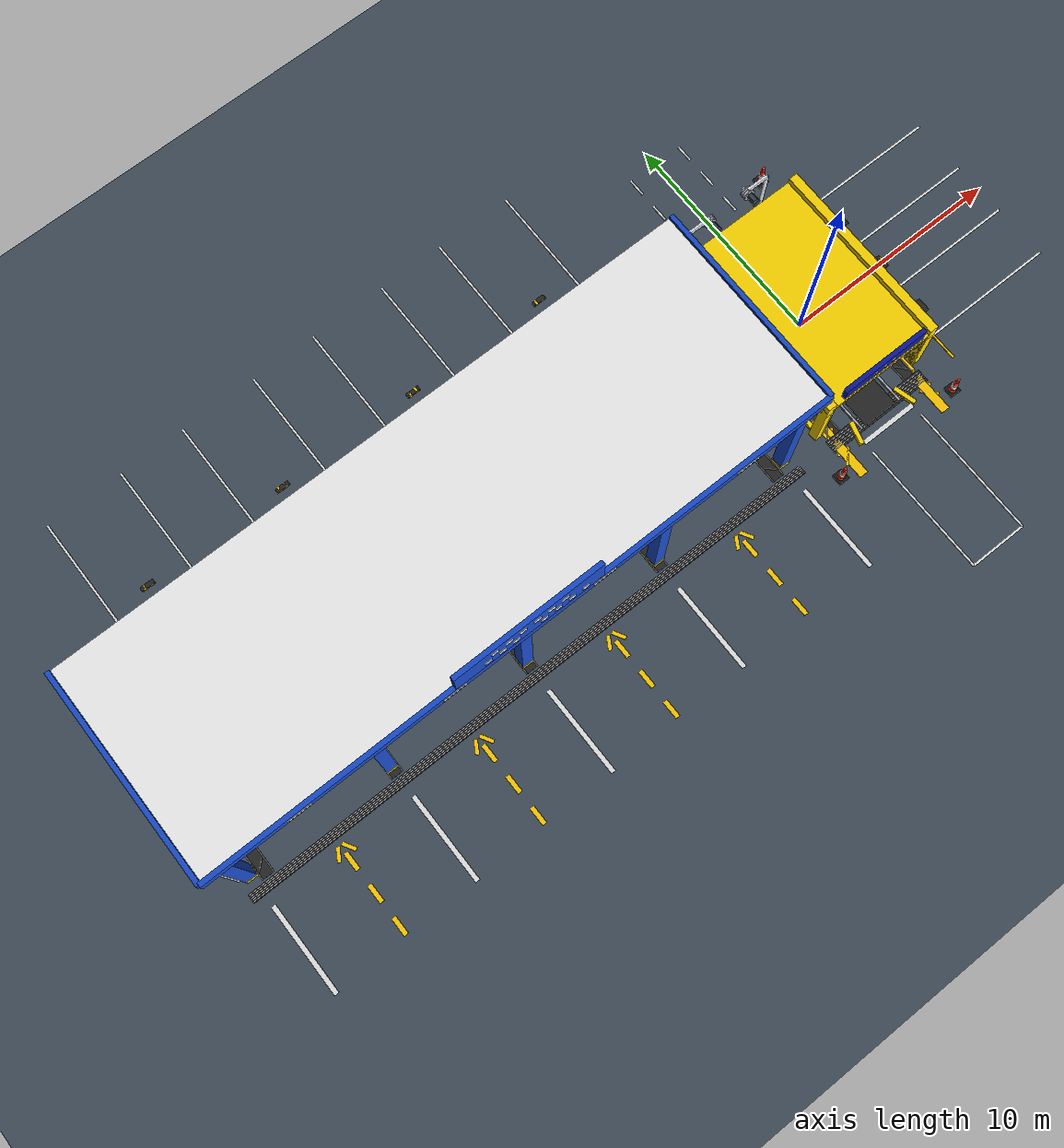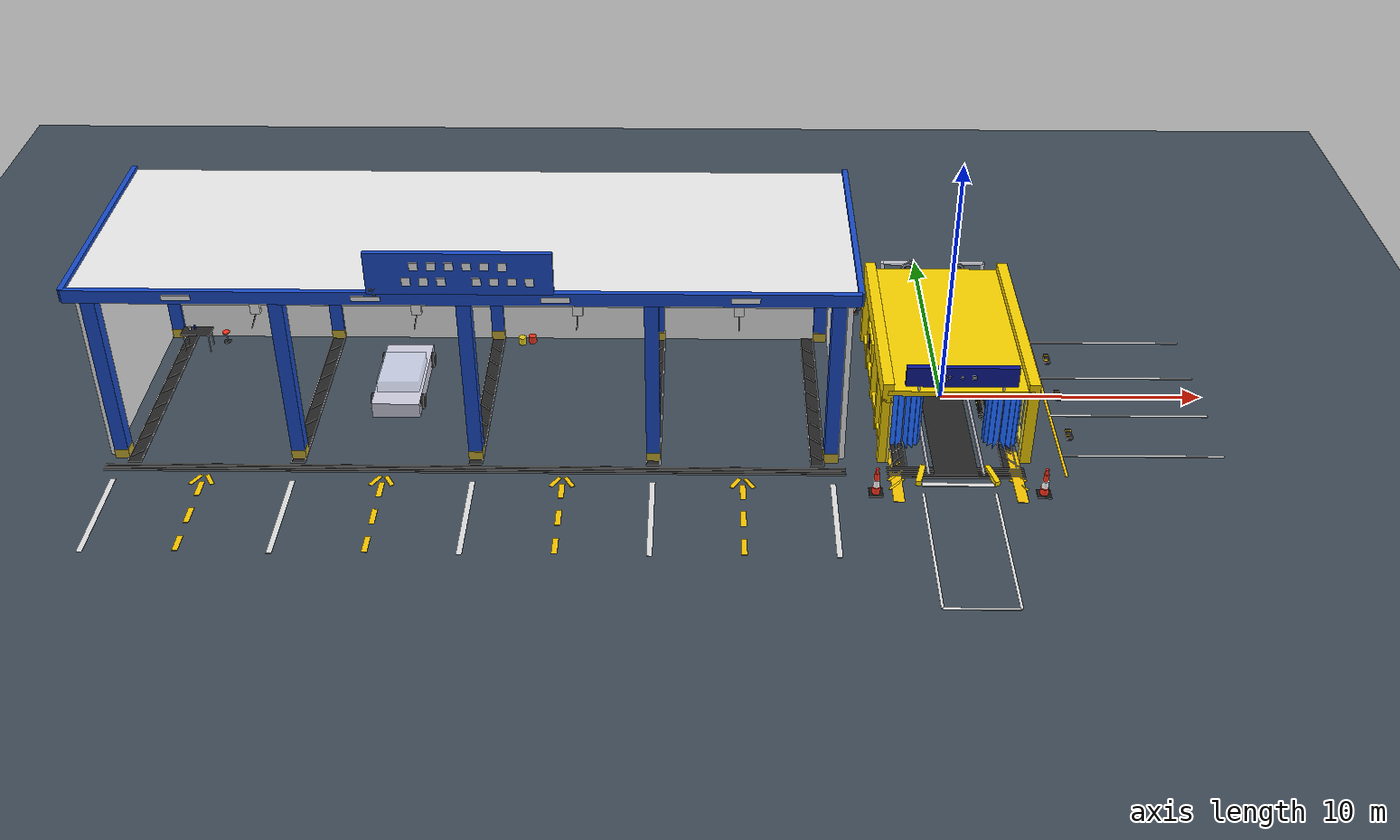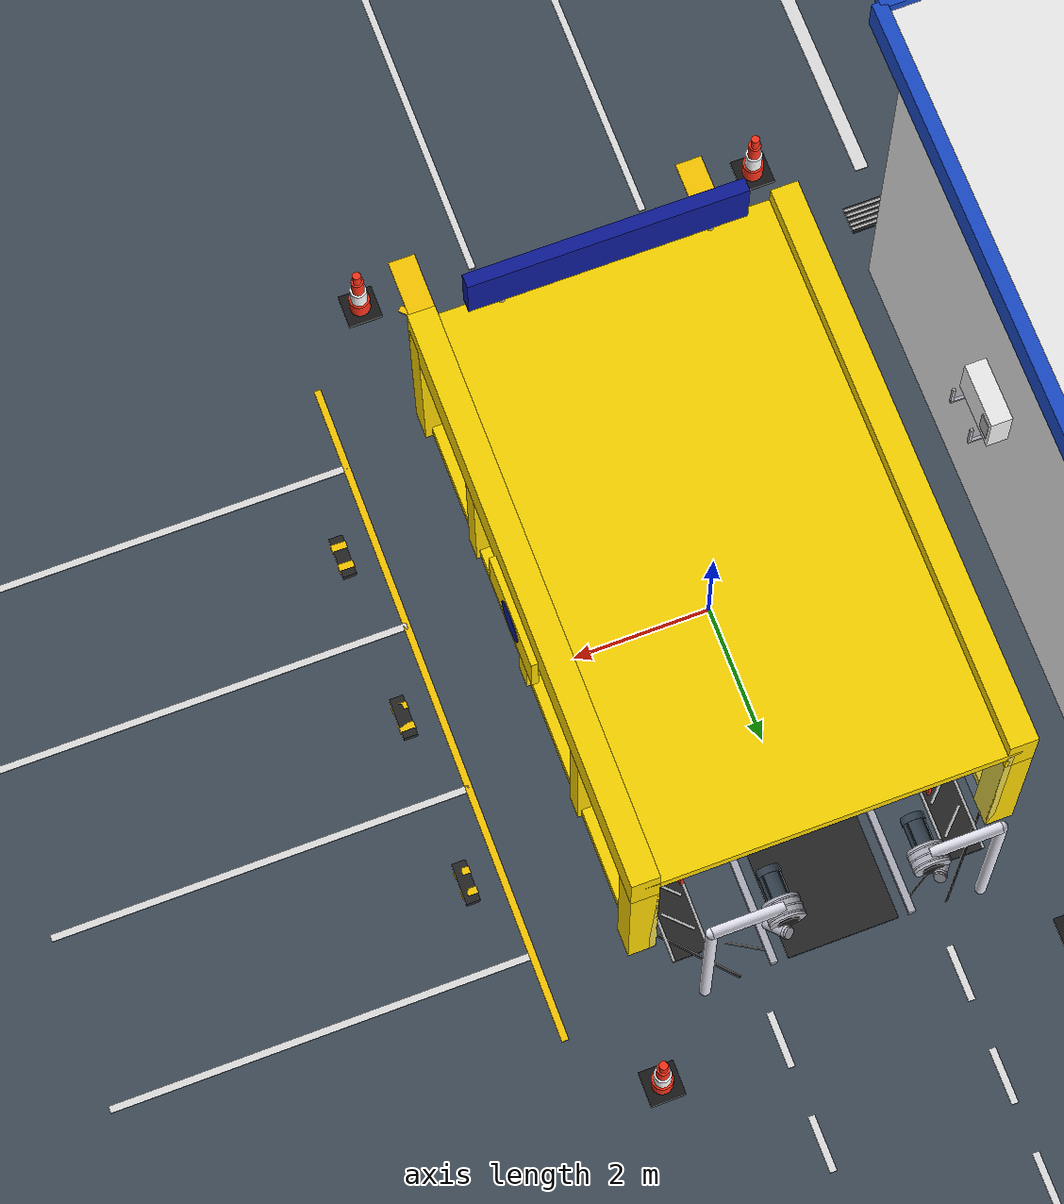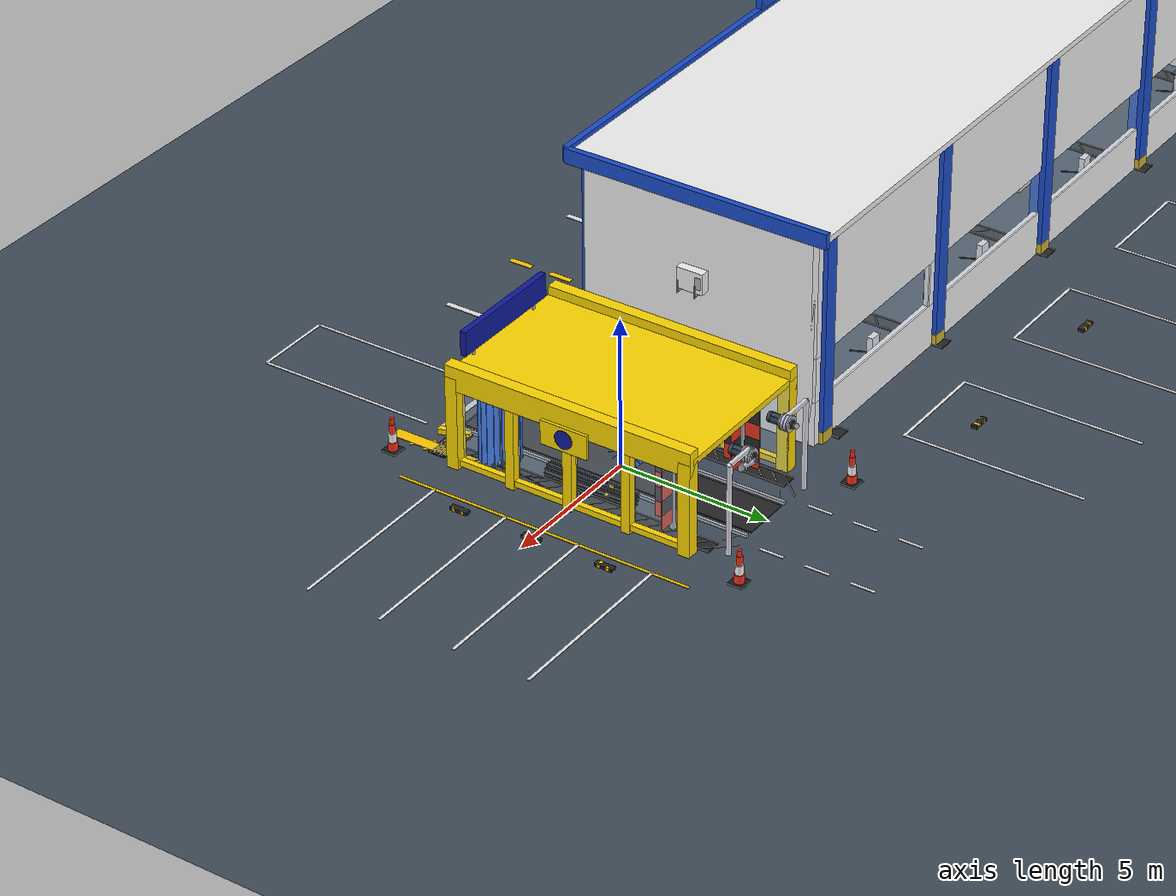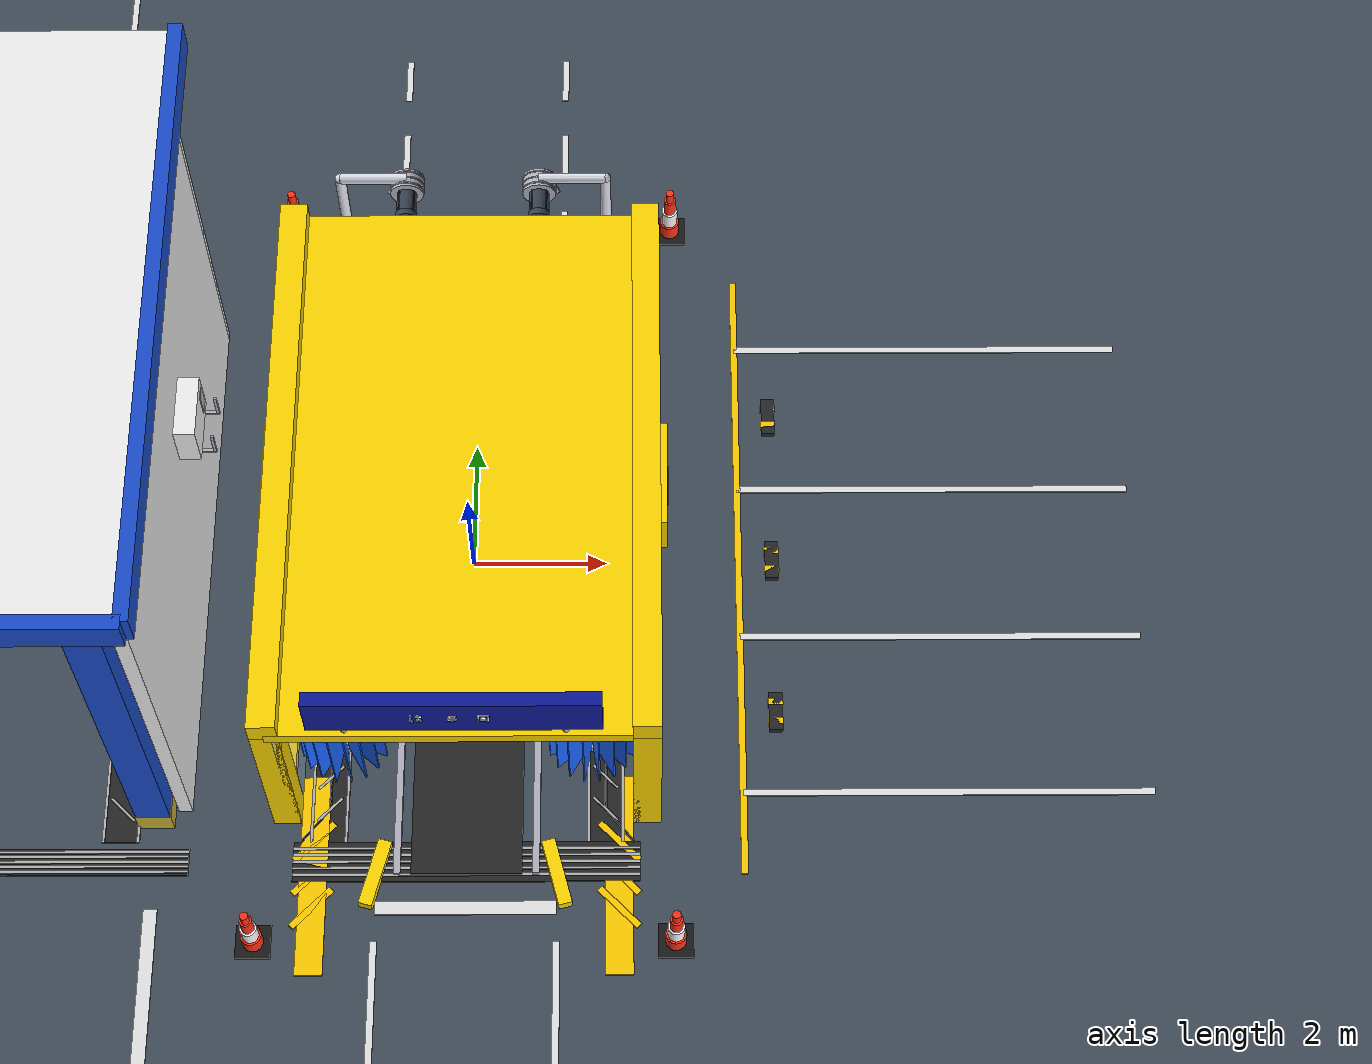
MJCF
<mujoco model="Tunnel Car Wash KSL">
    <compiler angle="degree" coordinate="local" inertiafromgeom="true"/>
    <option timestep="0.01" gravity="0 0 -9.81" density="1.2" viscosity="0.00002" integrator="RK4"/>

    <asset>
        <texture type="skybox" builtin="gradient" rgb1="0.4 0.6 0.8" rgb2="0.1 0.1 0.1" width="512" height="3072"/>
        <texture type="2d" name="groundplane" builtin="checker" rgb1="0.3 0.35 0.4" rgb2="0.2 0.25 0.3" width="512" height="512" mark="edge" markrgb="0.8 0.8 0.8"/>
        <material name="groundplane" texture="groundplane" texrepeat="20 20" texuniform="true" reflectance="0.2"/>

        <!-- Updated Colors based on KSL reference (Bright Yellow Tunnel) -->
        <material name="ksl_yellow" rgba="1.0 0.85 0.0 1" shininess="0.6" specular="0.4"/>
        <material name="ksl_logo_red" rgba="0.9 0.1 0.1 1" shininess="0.3"/>

        <!-- Brush Materials -->
        <material name="brush_red" rgba="0.9 0.2 0.1 1" shininess="0.1" specular="0.1"/>
        <material name="brush_black" rgba="0.15 0.15 0.15 1" shininess="0.1" specular="0.1"/>
        <material name="brush_blue" rgba="0.1 0.2 0.9 1" shininess="0.2"/>
        <material name="brush_yellow" rgba="0.9 0.8 0.1 1" shininess="0.2"/>
        <material name="brush_dark_blue" rgba="0.05 0.1 0.3 1" shininess="0.1" specular="0.1"/> <!-- New Dark Blue for brushes -->
        <material name="brush_mix" rgba="0.5 0.5 0.5 1" shininess="0.2"/> <!-- Placeholder for texture if needed -->

        <material name="steel" rgba="0.7 0.7 0.75 1" shininess="0.8" specular="0.8"/>
        <material name="black_plastic" rgba="0.1 0.1 0.1 1" shininess="0.3"/>
        <material name="conveyor_belt" rgba="0.15 0.15 0.15 1" shininess="0.1"/>

        <!-- Floor Markings -->
        <material name="paint_white" rgba="0.9 0.9 0.9 1" shininess="0.1" specular="0"/>
        <material name="paint_yellow" rgba="1.0 0.8 0.0 1" shininess="0.1" specular="0"/>

        <!-- Signboard Materials -->
        <material name="sign_board_blue" rgba="0.05 0.1 0.6 1" shininess="0.5"/>
        <material name="sign_text_white" rgba="1 1 1 1" shininess="0.8" emission="0.3"/>

        <!-- Glass Material -->
        <material name="glass" rgba="0.8 0.9 1.0 0.3" shininess="0.9" specular="0.9"/>

        <!-- Metal Grate Material -->
        <material name="metal_grate" rgba="0.7 0.7 0.7 1" shininess="0.5" specular="0.5"/>

        <!-- Rainbow Sign Materials -->
        <material name="rb_red" rgba="0.9 0.1 0.1 1" shininess="0.1"/>
        <material name="rb_orange" rgba="1.0 0.5 0.0 1" shininess="0.1"/>
        <material name="rb_yellow" rgba="1.0 0.9 0.0 1" shininess="0.1"/>
        <material name="rb_green" rgba="0.1 0.8 0.1 1" shininess="0.1"/>
        <material name="rb_blue" rgba="0.1 0.5 1.0 1" shininess="0.1"/>
        <material name="rb_cyan" rgba="0.0 1.0 1.0 1" shininess="0.5" emission="0.2"/> <!-- For drops -->
        <material name="sign_bg_dark" rgba="0.1 0.2 0.4 1" shininess="0.2"/>

        <!-- Dryer Materials -->
        <material name="dryer_white" rgba="0.9 0.9 0.95 1" shininess="0.5" specular="0.5"/>
        <material name="dryer_grill" rgba="0.1 0.1 0.1 1" shininess="0.5"/>
        <material name="cable_black" rgba="0.05 0.05 0.05 1" shininess="0.3"/>

        <!-- Traffic Cone Materials -->
        <material name="cone_red" rgba="1 0.2 0.1 1" shininess="0.5"/>
        <material name="cone_white" rgba="1 1 1 1" shininess="0.5" reflectance="0.5"/> <!-- Reflective tape -->
        <material name="cone_base" rgba="0.1 0.1 0.1 1" shininess="0.2"/>

        <!-- Industrial Blower Materials -->
        <material name="blower_metal" rgba="0.7 0.7 0.75 1" shininess="0.8" specular="0.8"/> <!-- Silver/Aluminum -->
        <material name="blower_motor" rgba="0.2 0.25 0.3 1" shininess="0.5"/> <!-- Dark Blue-Grey -->

        <!-- New Detailed Brush Materials -->
        <material name="brush_yellow_bright" rgba="1.0 0.9 0.0 1" shininess="0.3" specular="0.2"/>
        <material name="brush_blue_bright" rgba="0.1 0.4 1.0 1" shininess="0.3" specular="0.2"/>
        <material name="plastic_white" rgba="0.9 0.9 0.9 1" shininess="0.5"/>
        <texture name="camry_tex_paint" type="cube" builtin="flat" rgb1="0.9 0.9 0.95" width="100" height="100"/>
        <material name="camry_paint_silver" texture="camry_tex_paint" reflectance="0.6" shininess="0.9" rgba="0.92 0.92 0.95 1"/>
        <material name="camry_glass" reflectance="0.5" shininess="0.9" rgba="0.1 0.15 0.2 0.7"/>
        <material name="camry_rubber" reflectance="0.1" roughness="0.8" rgba="0.1 0.1 0.1 1"/>
        <material name="camry_chrome" reflectance="0.9" shininess="1.0" rgba="0.9 0.9 0.9 1"/>
        <material name="camry_rim_alloy" reflectance="0.7" shininess="0.8" rgba="0.7 0.7 0.75 1"/>
        <material name="camry_light_front" emission="15" rgba="0.9 0.9 1 1"/>
        <material name="camry_light_rear" emission="8" rgba="0.9 0 0 1"/>
        <material name="camry_grille_mat" reflectance="0.3" rgba="0.05 0.05 0.05 1"/>

        <!-- Manual Wash Bay Materials -->
        <material name="carshome_blue" rgba="0.1 0.3 0.8 1" shininess="0.5"/>
        <material name="carshome_white" rgba="0.95 0.95 0.95 1" shininess="0.5"/>
        <material name="floor_tile_blue" rgba="0.2 0.4 0.9 1" shininess="0.8" reflectance="0.3"/>
        <material name="floor_tile_yellow" rgba="1.0 0.8 0.1 1" shininess="0.5"/>
        <material name="gold_trim" rgba="0.8 0.7 0.2 1" shininess="0.8" specular="0.8"/>
    </asset>

    <worldbody>
        <light pos="8 -8 10" dir="-0.5 0.5 -1" castshadow="true" diffuse="0.9 0.9 0.9"/>
        <light pos="-8 8 10" dir="0.5 -0.5 -1" castshadow="false" diffuse="0.6 0.6 0.6"/>

        <geom name="floor" size="0 0 0.1" type="plane" material="groundplane"/>

        <!-- ==================== FLOOR MARKINGS ==================== -->
        <body name="floor_markings" pos="0 0 0.02">
            <!-- DRAINAGE GRATES -->
            <!-- Front Entrance Drain (Transverse) -->
            <geom name="drain_front_frame" type="box" size="2.5 0.3 0.02" pos="0 -4.8 -0.01" material="brush_black"/> <!-- Dark pit background -->
            <!-- Grate bars (Front) -->
            <geom type="box" size="2.5 0.02 0.02" pos="0 -4.6 0" material="metal_grate"/>
            <geom type="box" size="2.5 0.02 0.02" pos="0 -4.7 0" material="metal_grate"/>
            <geom type="box" size="2.5 0.02 0.02" pos="0 -4.8 0" material="metal_grate"/>
            <geom type="box" size="2.5 0.02 0.02" pos="0 -4.9 0" material="metal_grate"/>
            <geom type="box" size="2.5 0.02 0.02" pos="0 -5.0 0" material="metal_grate"/>

            <!-- Left Side Drain (Longitudinal) -->
            <geom name="drain_side_L_frame" type="box" size="0.25 4.5 0.02" pos="-2.0 0 -0.01" material="brush_black"/>
            <!-- Grate bars (Left) - angled for style -->
            <geom type="box" size="0.25 0.02 0.02" pos="-2.0 -4.0 0" euler="0 0 45" material="metal_grate"/>
            <geom type="box" size="0.25 0.02 0.02" pos="-2.0 -3.5 0" euler="0 0 45" material="metal_grate"/>
            <geom type="box" size="0.25 0.02 0.02" pos="-2.0 -3.0 0" euler="0 0 45" material="metal_grate"/>
            <geom type="box" size="0.25 0.02 0.02" pos="-2.0 -2.5 0" euler="0 0 45" material="metal_grate"/>
            <geom type="box" size="0.25 0.02 0.02" pos="-2.0 -2.0 0" euler="0 0 45" material="metal_grate"/>
            <geom type="box" size="0.25 0.02 0.02" pos="-2.0 -1.5 0" euler="0 0 45" material="metal_grate"/>
            <geom type="box" size="0.25 0.02 0.02" pos="-2.0 -1.0 0" euler="0 0 45" material="metal_grate"/>
            <geom type="box" size="0.25 0.02 0.02" pos="-2.0 -0.5 0" euler="0 0 45" material="metal_grate"/>
            <geom type="box" size="0.25 0.02 0.02" pos="-2.0 0.0 0" euler="0 0 45" material="metal_grate"/>
            <geom type="box" size="0.25 0.02 0.02" pos="-2.0 0.5 0" euler="0 0 45" material="metal_grate"/>
            <geom type="box" size="0.25 0.02 0.02" pos="-2.0 1.0 0" euler="0 0 45" material="metal_grate"/>
            <geom type="box" size="0.25 0.02 0.02" pos="-2.0 1.5 0" euler="0 0 45" material="metal_grate"/>
            <geom type="box" size="0.25 0.02 0.02" pos="-2.0 2.0 0" euler="0 0 45" material="metal_grate"/>
            <geom type="box" size="0.25 0.02 0.02" pos="-2.0 2.5 0" euler="0 0 45" material="metal_grate"/>
            <geom type="box" size="0.25 0.02 0.02" pos="-2.0 3.0 0" euler="0 0 45" material="metal_grate"/>
            <geom type="box" size="0.25 0.02 0.02" pos="-2.0 3.5 0" euler="0 0 45" material="metal_grate"/>
            <geom type="box" size="0.25 0.02 0.02" pos="-2.0 4.0 0" euler="0 0 45" material="metal_grate"/>
            <!-- Side rails for drain -->
            <geom type="box" size="0.02 4.5 0.02" pos="-1.75 0 0" material="metal_grate"/>
            <geom type="box" size="0.02 4.5 0.02" pos="-2.25 0 0" material="metal_grate"/>

            <!-- Right Side Drain (Longitudinal) -->
            <geom name="drain_side_R_frame" type="box" size="0.25 4.5 0.02" pos="2.0 0 -0.01" material="brush_black"/>
            <!-- Grate bars (Right) -->
            <geom type="box" size="0.25 0.02 0.02" pos="2.0 -4.0 0" euler="0 0 -45" material="metal_grate"/>
            <geom type="box" size="0.25 0.02 0.02" pos="2.0 -3.5 0" euler="0 0 -45" material="metal_grate"/>
            <geom type="box" size="0.25 0.02 0.02" pos="2.0 -3.0 0" euler="0 0 -45" material="metal_grate"/>
            <geom type="box" size="0.25 0.02 0.02" pos="2.0 -2.5 0" euler="0 0 -45" material="metal_grate"/>
            <geom type="box" size="0.25 0.02 0.02" pos="2.0 -2.0 0" euler="0 0 -45" material="metal_grate"/>
            <geom type="box" size="0.25 0.02 0.02" pos="2.0 -1.5 0" euler="0 0 -45" material="metal_grate"/>
            <geom type="box" size="0.25 0.02 0.02" pos="2.0 -1.0 0" euler="0 0 -45" material="metal_grate"/>
            <geom type="box" size="0.25 0.02 0.02" pos="2.0 -0.5 0" euler="0 0 -45" material="metal_grate"/>
            <geom type="box" size="0.25 0.02 0.02" pos="2.0 0.0 0" euler="0 0 -45" material="metal_grate"/>
            <geom type="box" size="0.25 0.02 0.02" pos="2.0 0.5 0" euler="0 0 -45" material="metal_grate"/>
            <geom type="box" size="0.25 0.02 0.02" pos="2.0 1.0 0" euler="0 0 -45" material="metal_grate"/>
            <geom type="box" size="0.25 0.02 0.02" pos="2.0 1.5 0" euler="0 0 -45" material="metal_grate"/>
            <geom type="box" size="0.25 0.02 0.02" pos="2.0 2.0 0" euler="0 0 -45" material="metal_grate"/>
            <geom type="box" size="0.25 0.02 0.02" pos="2.0 2.5 0" euler="0 0 -45" material="metal_grate"/>
            <geom type="box" size="0.25 0.02 0.02" pos="2.0 3.0 0" euler="0 0 -45" material="metal_grate"/>
            <geom type="box" size="0.25 0.02 0.02" pos="2.0 3.5 0" euler="0 0 -45" material="metal_grate"/>
            <geom type="box" size="0.25 0.02 0.02" pos="2.0 4.0 0" euler="0 0 -45" material="metal_grate"/>
            <!-- Side rails for drain -->
            <geom type="box" size="0.02 4.5 0.02" pos="1.75 0 0" material="metal_grate"/>
            <geom type="box" size="0.02 4.5 0.02" pos="2.25 0 0" material="metal_grate"/>

            <!-- Parking/Queue Lane (White) -->
            <!-- Left Lane Line (Longitudinal) -->
            <geom name="line_lane_L" type="box" size="0.05 3 0.01" pos="-1.3 -9 0" material="paint_white"/>
            <!-- Right Lane Line (Longitudinal) -->
            <geom name="line_lane_R" type="box" size="0.05 3 0.01" pos="1.3 -9 0" material="paint_white"/>
            <!-- Stop Line (Transverse) -->
            <geom name="line_stop" type="box" size="1.3 0.1 0.01" pos="0 -5.5 0" material="paint_white"/>
            <!-- Back Parking Box Line -->
            <geom name="line_park_back" type="box" size="1.3 0.05 0.01" pos="0 -12 0" material="paint_white"/>

            <!-- Safety Zones (Yellow) - Near Entrance -->
            <!-- Left Safety Strip -->
            <geom name="safety_L" type="box" size="0.2 1.5 0.01" pos="-2.2 -5.0 0" material="paint_yellow"/>
            <!-- Right Safety Strip -->
            <geom name="safety_R" type="box" size="0.2 1.5 0.01" pos="2.2 -5.0 0" material="paint_yellow"/>

            <!-- Diagonal Hazard Stripes -->
            <geom name="hatch_L1" type="box" size="0.4 0.05 0.01" pos="-2.2 -5.5 0" euler="0 0 45" material="paint_yellow"/>
            <geom name="hatch_L2" type="box" size="0.4 0.05 0.01" pos="-2.2 -5.0 0" euler="0 0 45" material="paint_yellow"/>
            <geom name="hatch_L3" type="box" size="0.4 0.05 0.01" pos="-2.2 -4.5 0" euler="0 0 45" material="paint_yellow"/>

            <geom name="hatch_R1" type="box" size="0.4 0.05 0.01" pos="2.2 -5.5 0" euler="0 0 -45" material="paint_yellow"/>
            <geom name="hatch_R2" type="box" size="0.4 0.05 0.01" pos="2.2 -5.0 0" euler="0 0 -45" material="paint_yellow"/>
            <geom name="hatch_R3" type="box" size="0.4 0.05 0.01" pos="2.2 -4.5 0" euler="0 0 -45" material="paint_yellow"/>

            <!-- PARKING SPACES (Right Side) -->
            <!-- Yellow Lane Line -->
            <geom name="park_lane_line" type="box" size="0.05 5.0 0.01" pos="4.0 0 0" material="paint_yellow"/>

            <!-- Spot 1 (Top) -->
            <geom name="park_line_1" type="box" size="3.0 0.05 0.01" pos="7.0 3.75 0" material="paint_white"/>
            <geom name="park_line_2" type="box" size="3.0 0.05 0.01" pos="7.0 1.25 0" material="paint_white"/>
            <geom name="stopper_1_base" type="box" size="0.1 0.3 0.05" pos="4.5 2.5 0.05" material="brush_black"/>
            <geom name="stopper_1_y1" type="box" size="0.11 0.05 0.05" pos="4.5 2.35 0.05" material="paint_yellow"/>
            <geom name="stopper_1_y2" type="box" size="0.11 0.05 0.05" pos="4.5 2.65 0.05" material="paint_yellow"/>

            <!-- Spot 2 (Middle) -->
            <geom name="park_line_3" type="box" size="3.0 0.05 0.01" pos="7.0 -1.25 0" material="paint_white"/>
            <geom name="stopper_2_base" type="box" size="0.1 0.3 0.05" pos="4.5 0.0 0.05" material="brush_black"/>
            <geom name="stopper_2_y1" type="box" size="0.11 0.05 0.05" pos="4.5 -0.15 0.05" material="paint_yellow"/>
            <geom name="stopper_2_y2" type="box" size="0.11 0.05 0.05" pos="4.5 0.15 0.05" material="paint_yellow"/>

            <!-- Spot 3 (Bottom) -->
            <geom name="park_line_4" type="box" size="3.0 0.05 0.01" pos="7.0 -3.75 0" material="paint_white"/>
            <geom name="stopper_3_base" type="box" size="0.1 0.3 0.05" pos="4.5 -2.5 0.05" material="brush_black"/>
            <geom name="stopper_3_y1" type="box" size="0.11 0.05 0.05" pos="4.5 -2.65 0.05" material="paint_yellow"/>
            <geom name="stopper_3_y2" type="box" size="0.11 0.05 0.05" pos="4.5 -2.35 0.05" material="paint_yellow"/>

            <!-- Exit Guide Lines (Dashed White) -->
            <geom name="guide_L1" type="box" size="0.05 0.4 0.01" pos="-1.3 6.0 0" material="paint_white"/>
            <geom name="guide_L2" type="box" size="0.05 0.4 0.01" pos="-1.3 7.5 0" material="paint_white"/>
            <geom name="guide_L3" type="box" size="0.05 0.4 0.01" pos="-1.3 9.0 0" material="paint_white"/>

            <geom name="guide_R1" type="box" size="0.05 0.4 0.01" pos="1.3 6.0 0" material="paint_white"/>
            <geom name="guide_R2" type="box" size="0.05 0.4 0.01" pos="1.3 7.5 0" material="paint_white"/>
            <geom name="guide_R3" type="box" size="0.05 0.4 0.01" pos="1.3 9.0 0" material="paint_white"/>
        </body>

        <!-- CAMRY REMOVED -->

        <!-- ==================== TUNNEL STRUCTURE ==================== -->
        <!-- The tunnel is longer now, approximately 8 meters long (y: -4 to 4) -->
        <body name="tunnel_frame" pos="0 0 0">
            <!-- ROOF -->
            <geom name="roof_plate" type="box" size="2.6 4.2 0.1" pos="0 0 3.1" material="ksl_yellow"/>
            <geom name="roof_side_L" type="box" size="0.2 4.2 0.4" pos="-2.6 0 3.1" material="ksl_yellow"/>
            <geom name="roof_side_R" type="box" size="0.2 4.2 0.4" pos="2.6 0 3.1" material="ksl_yellow"/>

            <!-- ================= MANUAL WASH BAY (Left Side - Expanded 4 Bays) ================= -->
            <!-- Position: Shifted further left to accommodate double width (Width ~14m) -->
            <!-- Center at -11.0 ensures right edge is at ~ -4.0, similar to before -->
            <body name="manual_wash_bay" pos="-17.5 0 0">

                <!-- 1. FLOORING -->
                <!-- Main Floor Base removed to expose original ground -->

                <!-- Yellow Bay Frames REMOVED -->
                <!-- Double Bay 1 (Right Side) -->
                <!-- Inner Grid Pattern Bay 1 -->

                <!-- Double Bay 2 (Left Side) -->
                <!-- Inner Grid Pattern Bay 2 -->

                <!-- 2. STRUCTURE COLUMNS (5 Pairs - Height 7.2m) -->
                <!-- Front Pillars -->
                <geom name="col_F_1" type="box" size="0.25 0.25 3.6" pos="-13.0 -4.0 3.6" material="carshome_blue"/>
                <geom name="col_F_2" type="box" size="0.25 0.25 3.6" pos="-6.5 -4.0 3.6" material="carshome_blue"/>
                <geom name="col_F_3" type="box" size="0.25 0.25 3.6" pos="0 -4.0 3.6" material="carshome_blue"/>
                <geom name="col_F_4" type="box" size="0.25 0.25 3.6" pos="6.5 -4.0 3.6" material="carshome_blue"/>
                <geom name="col_F_5" type="box" size="0.25 0.25 3.6" pos="13.0 -4.0 3.6" material="carshome_blue"/>

                <!-- Gold Trim Front -->
                <geom name="trim_F_1" type="box" size="0.26 0.26 0.2" pos="-13.0 -4.0 0.2" material="gold_trim"/>
                <geom name="trim_F_2" type="box" size="0.26 0.26 0.2" pos="-6.5 -4.0 0.2" material="gold_trim"/>
                <geom name="trim_F_3" type="box" size="0.26 0.26 0.2" pos="0 -4.0 0.2" material="gold_trim"/>
                <geom name="trim_F_4" type="box" size="0.26 0.26 0.2" pos="6.5 -4.0 0.2" material="gold_trim"/>
                <geom name="trim_F_5" type="box" size="0.26 0.26 0.2" pos="13.0 -4.0 0.2" material="gold_trim"/>

                <!-- Back Pillars -->
                <geom name="col_B_1" type="box" size="0.25 0.25 3.6" pos="-13.0 4.0 3.6" material="carshome_blue"/>
                <geom name="col_B_2" type="box" size="0.25 0.25 3.6" pos="-6.5 4.0 3.6" material="carshome_blue"/>
                <geom name="col_B_3" type="box" size="0.25 0.25 3.6" pos="0 4.0 3.6" material="carshome_blue"/>
                <geom name="col_B_4" type="box" size="0.25 0.25 3.6" pos="6.5 4.0 3.6" material="carshome_blue"/>
                <geom name="col_B_5" type="box" size="0.25 0.25 3.6" pos="13.0 4.0 3.6" material="carshome_blue"/>

                <geom name="trim_B_1" type="box" size="0.26 0.26 0.2" pos="-13.0 4.0 0.2" material="gold_trim"/>
                <geom name="trim_B_2" type="box" size="0.26 0.26 0.2" pos="-6.5 4.0 0.2" material="gold_trim"/>
                <geom name="trim_B_3" type="box" size="0.26 0.26 0.2" pos="0 4.0 0.2" material="gold_trim"/>
                <geom name="trim_B_4" type="box" size="0.26 0.26 0.2" pos="6.5 4.0 0.2" material="gold_trim"/>
                <geom name="trim_B_5" type="box" size="0.26 0.26 0.2" pos="13.0 4.0 0.2" material="gold_trim"/>

                <!-- 3. WALLS (Interior White - Height Increased to 7.2m) -->
                <!-- Back Wall split into sections to allow for windows -->
                <!-- Windows will be placed at height 1.5m to 3.0m -->
                <!-- Lower Wall (0 to 1.5m) -->
                <geom name="bay_wall_back_low" type="box" size="13.5 0.1 0.75" pos="0 4.0 0.75" material="carshome_white"/>
                <!-- Upper Wall (3.0m to 7.2m) -->
                <geom name="bay_wall_back_high" type="box" size="13.5 0.1 2.1" pos="0 4.0 5.1" material="carshome_white"/>

                <!-- Vertical Columns between windows (at -13.5, -6.75, 0, 6.75, 13.5) -->
                <geom name="bay_wall_col_1" type="box" size="0.25 0.1 0.75" pos="-13.25 4.0 2.25" material="carshome_white"/>
                <geom name="bay_wall_col_2" type="box" size="0.25 0.1 0.75" pos="-6.75 4.0 2.25" material="carshome_white"/>
                <geom name="bay_wall_col_3" type="box" size="0.25 0.1 0.75" pos="0 4.0 2.25" material="carshome_white"/>
                <geom name="bay_wall_col_4" type="box" size="0.25 0.1 0.75" pos="6.75 4.0 2.25" material="carshome_white"/>
                <geom name="bay_wall_col_5" type="box" size="0.25 0.1 0.75" pos="13.25 4.0 2.25" material="carshome_white"/>

                <!-- Windows (Glass) -->
                <!-- Window 1 (Leftmost) -->
                <geom name="window_1" type="box" size="3.125 0.05 0.75" pos="-10.0 4.0 2.25" material="glass"/>
                <!-- Window 2 (Left-Center) -->
                <geom name="window_2" type="box" size="3.125 0.05 0.75" pos="-3.375 4.0 2.25" material="glass"/>
                <!-- Window 3 (Right-Center) -->
                <geom name="window_3" type="box" size="3.125 0.05 0.75" pos="3.375 4.0 2.25" material="glass"/>
                <!-- Window 4 (Rightmost) -->
                <geom name="window_4" type="box" size="3.125 0.05 0.75" pos="10.0 4.0 2.25" material="glass"/>

                <geom name="bay_wall_L" type="box" size="0.1 4.0 3.6" pos="-13.4 0 3.6" material="carshome_white"/>
                <geom name="bay_wall_R" type="box" size="0.1 4.0 3.6" pos="13.4 0 3.6" material="carshome_white"/>

                <!-- 4. ROOF (Raised to 7.2m) -->
                <geom name="bay_roof" type="box" size="13.7 4.5 0.1" pos="0 0 7.2" material="carshome_white"/>
                <!-- Fascia -->
                <geom name="bay_fascia_F" type="box" size="13.7 0.1 0.25" pos="0 -4.5 7.2" material="carshome_blue"/>
                <geom name="bay_fascia_L" type="box" size="0.1 4.5 0.25" pos="-13.7 0 7.2" material="carshome_blue"/>
                <geom name="bay_fascia_R" type="box" size="0.1 4.5 0.25" pos="13.7 0 7.2" material="carshome_blue"/>

                <!-- Simulated Text "Carshome" - Distributed -->
                <geom name="logo_text_1" type="box" size="0.5 0.02 0.1" pos="-9.75 -4.6 7.2" material="carshome_white"/>
                <geom name="logo_text_2" type="box" size="0.5 0.02 0.1" pos="-3.25 -4.6 7.2" material="carshome_white"/>
                <geom name="logo_text_3" type="box" size="0.5 0.02 0.1" pos="3.25 -4.6 7.2" material="carshome_white"/>
                <geom name="logo_text_4" type="box" size="0.5 0.02 0.1" pos="9.75 -4.6 7.2" material="carshome_white"/>

                <!-- DOORS REMOVED -->

                <!-- 5. DRAINAGE CHANNEL -->
                <!-- Front Drain (Detailed) -->
                <geom name="bay_drain_frame" type="box" size="13.5 0.2 0.02" pos="0 -4.8 0.02" material="brush_black"/>
                <!-- Grate bars (Parallel) - Stretched -->
                <geom type="box" size="13.5 0.02 0.02" pos="0 -4.65 0.04" material="metal_grate"/>
                <geom type="box" size="13.5 0.02 0.02" pos="0 -4.72 0.04" material="metal_grate"/>
                <geom type="box" size="13.5 0.02 0.02" pos="0 -4.80 0.04" material="metal_grate"/>
                <geom type="box" size="13.5 0.02 0.02" pos="0 -4.87 0.04" material="metal_grate"/>
                <geom type="box" size="13.5 0.02 0.02" pos="0 -4.95 0.04" material="metal_grate"/>

                <!-- Side Drains (Left & Right) -->
                <!-- Left Side Drain -->
                <geom name="bay_drain_L_frame" type="box" size="0.25 4.5 0.02" pos="-12.5 0 0.02" material="brush_black"/>
                <!-- Grate Bars Left -->
                <geom type="box" size="0.25 0.02 0.02" pos="-12.5 -4.0 0.04" euler="0 0 45" material="metal_grate"/>
                <geom type="box" size="0.25 0.02 0.02" pos="-12.5 -3.0 0.04" euler="0 0 45" material="metal_grate"/>
                <geom type="box" size="0.25 0.02 0.02" pos="-12.5 -2.0 0.04" euler="0 0 45" material="metal_grate"/>
                <geom type="box" size="0.25 0.02 0.02" pos="-12.5 -1.0 0.04" euler="0 0 45" material="metal_grate"/>
                <geom type="box" size="0.25 0.02 0.02" pos="-12.5 0.0 0.04" euler="0 0 45" material="metal_grate"/>
                <geom type="box" size="0.25 0.02 0.02" pos="-12.5 1.0 0.04" euler="0 0 45" material="metal_grate"/>
                <geom type="box" size="0.25 0.02 0.02" pos="-12.5 2.0 0.04" euler="0 0 45" material="metal_grate"/>
                <geom type="box" size="0.25 0.02 0.02" pos="-12.5 3.0 0.04" euler="0 0 45" material="metal_grate"/>
                <geom type="box" size="0.25 0.02 0.02" pos="-12.5 4.0 0.04" euler="0 0 45" material="metal_grate"/>
                <!-- Longitudinal rails Left -->
                <geom type="box" size="0.02 4.5 0.02" pos="-12.75 0 0.04" material="metal_grate"/>
                <geom type="box" size="0.02 4.5 0.02" pos="-12.25 0 0.04" material="metal_grate"/>

                <!-- Right Side Drain -->
                <geom name="bay_drain_R_frame" type="box" size="0.25 4.5 0.02" pos="12.5 0 0.02" material="brush_black"/>
                <!-- Grate Bars Right -->
                <geom type="box" size="0.25 0.02 0.02" pos="12.5 -4.0 0.04" euler="0 0 -45" material="metal_grate"/>
                <geom type="box" size="0.25 0.02 0.02" pos="12.5 -3.0 0.04" euler="0 0 -45" material="metal_grate"/>
                <geom type="box" size="0.25 0.02 0.02" pos="12.5 -2.0 0.04" euler="0 0 -45" material="metal_grate"/>
                <geom type="box" size="0.25 0.02 0.02" pos="12.5 -1.0 0.04" euler="0 0 -45" material="metal_grate"/>
                <geom type="box" size="0.25 0.02 0.02" pos="12.5 0.0 0.04" euler="0 0 -45" material="metal_grate"/>
                <geom type="box" size="0.25 0.02 0.02" pos="12.5 1.0 0.04" euler="0 0 -45" material="metal_grate"/>
                <geom type="box" size="0.25 0.02 0.02" pos="12.5 2.0 0.04" euler="0 0 -45" material="metal_grate"/>
                <geom type="box" size="0.25 0.02 0.02" pos="12.5 3.0 0.04" euler="0 0 -45" material="metal_grate"/>
                <geom type="box" size="0.25 0.02 0.02" pos="12.5 4.0 0.04" euler="0 0 -45" material="metal_grate"/>
                <!-- Longitudinal rails Right -->
                <geom type="box" size="0.02 4.5 0.02" pos="12.75 0 0.04" material="metal_grate"/>
                <geom type="box" size="0.02 4.5 0.02" pos="12.25 0 0.04" material="metal_grate"/>

                <!-- Middle Drains (Behind Intermediate Pillars) -->
                <!-- Drain 1 (at x = -6.5) -->
                <geom name="bay_drain_M1_frame" type="box" size="0.25 4.5 0.02" pos="-6.5 0 0.02" material="brush_black"/>
                <geom type="box" size="0.25 0.02 0.02" pos="-6.5 -4.0 0.04" euler="0 0 45" material="metal_grate"/>
                <geom type="box" size="0.25 0.02 0.02" pos="-6.5 -3.0 0.04" euler="0 0 45" material="metal_grate"/>
                <geom type="box" size="0.25 0.02 0.02" pos="-6.5 -2.0 0.04" euler="0 0 45" material="metal_grate"/>
                <geom type="box" size="0.25 0.02 0.02" pos="-6.5 -1.0 0.04" euler="0 0 45" material="metal_grate"/>
                <geom type="box" size="0.25 0.02 0.02" pos="-6.5 0.0 0.04" euler="0 0 45" material="metal_grate"/>
                <geom type="box" size="0.25 0.02 0.02" pos="-6.5 1.0 0.04" euler="0 0 45" material="metal_grate"/>
                <geom type="box" size="0.25 0.02 0.02" pos="-6.5 2.0 0.04" euler="0 0 45" material="metal_grate"/>
                <geom type="box" size="0.25 0.02 0.02" pos="-6.5 3.0 0.04" euler="0 0 45" material="metal_grate"/>
                <geom type="box" size="0.25 0.02 0.02" pos="-6.5 4.0 0.04" euler="0 0 45" material="metal_grate"/>
                <geom type="box" size="0.02 4.5 0.02" pos="-6.75 0 0.04" material="metal_grate"/>
                <geom type="box" size="0.02 4.5 0.02" pos="-6.25 0 0.04" material="metal_grate"/>

                <!-- Drain 2 (at x = 0) -->
                <geom name="bay_drain_M2_frame" type="box" size="0.25 4.5 0.02" pos="0 0 0.02" material="brush_black"/>
                <geom type="box" size="0.25 0.02 0.02" pos="0 -4.0 0.04" euler="0 0 -45" material="metal_grate"/>
                <geom type="box" size="0.25 0.02 0.02" pos="0 -3.0 0.04" euler="0 0 -45" material="metal_grate"/>
                <geom type="box" size="0.25 0.02 0.02" pos="0 -2.0 0.04" euler="0 0 -45" material="metal_grate"/>
                <geom type="box" size="0.25 0.02 0.02" pos="0 -1.0 0.04" euler="0 0 -45" material="metal_grate"/>
                <geom type="box" size="0.25 0.02 0.02" pos="0 0.0 0.04" euler="0 0 -45" material="metal_grate"/>
                <geom type="box" size="0.25 0.02 0.02" pos="0 1.0 0.04" euler="0 0 -45" material="metal_grate"/>
                <geom type="box" size="0.25 0.02 0.02" pos="0 2.0 0.04" euler="0 0 -45" material="metal_grate"/>
                <geom type="box" size="0.25 0.02 0.02" pos="0 3.0 0.04" euler="0 0 -45" material="metal_grate"/>
                <geom type="box" size="0.25 0.02 0.02" pos="0 4.0 0.04" euler="0 0 -45" material="metal_grate"/>
                <geom type="box" size="0.02 4.5 0.02" pos="-0.25 0 0.04" material="metal_grate"/>
                <geom type="box" size="0.02 4.5 0.02" pos="0.25 0 0.04" material="metal_grate"/>

                <!-- Drain 3 (at x = 6.5) -->
                <geom name="bay_drain_M3_frame" type="box" size="0.25 4.5 0.02" pos="6.5 0 0.02" material="brush_black"/>
                <geom type="box" size="0.25 0.02 0.02" pos="6.5 -4.0 0.04" euler="0 0 45" material="metal_grate"/>
                <geom type="box" size="0.25 0.02 0.02" pos="6.5 -3.0 0.04" euler="0 0 45" material="metal_grate"/>
                <geom type="box" size="0.25 0.02 0.02" pos="6.5 -2.0 0.04" euler="0 0 45" material="metal_grate"/>
                <geom type="box" size="0.25 0.02 0.02" pos="6.5 -1.0 0.04" euler="0 0 45" material="metal_grate"/>
                <geom type="box" size="0.25 0.02 0.02" pos="6.5 0.0 0.04" euler="0 0 45" material="metal_grate"/>
                <geom type="box" size="0.25 0.02 0.02" pos="6.5 1.0 0.04" euler="0 0 45" material="metal_grate"/>
                <geom type="box" size="0.25 0.02 0.02" pos="6.5 2.0 0.04" euler="0 0 45" material="metal_grate"/>
                <geom type="box" size="0.25 0.02 0.02" pos="6.5 3.0 0.04" euler="0 0 45" material="metal_grate"/>
                <geom type="box" size="0.25 0.02 0.02" pos="6.5 4.0 0.04" euler="0 0 45" material="metal_grate"/>
                <geom type="box" size="0.02 4.5 0.02" pos="6.25 0 0.04" material="metal_grate"/>
                <geom type="box" size="0.02 4.5 0.02" pos="6.75 0 0.04" material="metal_grate"/>

                <!-- 6. EQUIPMENT (4 Bays) -->
                <geom name="equip_box_1" type="box" size="0.2 0.1 0.3" pos="-9.75 3.8 1.5" material="carshome_white"/>
                <geom name="hose_1" type="capsule" fromto="-9.75 3.8 1.2 -9.75 3.0 1.0" size="0.02" material="brush_black"/>

                <geom name="equip_box_2" type="box" size="0.2 0.1 0.3" pos="-3.25 3.8 1.5" material="carshome_white"/>
                <geom name="hose_2" type="capsule" fromto="-3.25 3.8 1.2 -3.25 3.0 1.0" size="0.02" material="brush_black"/>

                <geom name="equip_box_3" type="box" size="0.2 0.1 0.3" pos="3.25 3.8 1.5" material="carshome_white"/>
                <geom name="hose_3" type="capsule" fromto="3.25 3.8 1.2 3.25 3.0 1.0" size="0.02" material="brush_black"/>

                <geom name="equip_box_4" type="box" size="0.2 0.1 0.3" pos="9.75 3.8 1.5" material="carshome_white"/>
                <geom name="hose_4" type="capsule" fromto="9.75 3.8 1.2 9.75 3.0 1.0" size="0.02" material="brush_black"/>

                <!-- 7. GROUND GUIDE LINES (Front) -->
                <!-- White Divider Lines (Between Bays) -->
                <geom name="line_div_1" type="box" size="0.1 2.0 0.01" pos="-13.0 -7.5 0.01" material="paint_white"/>
                <geom name="line_div_2" type="box" size="0.1 2.0 0.01" pos="-6.5 -7.5 0.01" material="paint_white"/>
                <geom name="line_div_3" type="box" size="0.1 2.0 0.01" pos="0 -7.5 0.01" material="paint_white"/>
                <geom name="line_div_4" type="box" size="0.1 2.0 0.01" pos="6.5 -7.5 0.01" material="paint_white"/>
                <geom name="line_div_5" type="box" size="0.1 2.0 0.01" pos="13.0 -7.5 0.01" material="paint_white"/>

                <!-- Yellow Center Guide Lines (Dashed + Arrow) -->
                <!-- Bay 1 (Left) -->
                <geom name="guide_1_1" type="box" size="0.1 0.4 0.01" pos="-9.75 -6.0 0.01" material="paint_yellow"/>
                <geom name="guide_1_2" type="box" size="0.1 0.4 0.01" pos="-9.75 -7.5 0.01" material="paint_yellow"/>
                <geom name="guide_1_3" type="box" size="0.1 0.4 0.01" pos="-9.75 -9.0 0.01" material="paint_yellow"/>
                <!-- Arrow Head 1 -->
                <geom name="arrow_1_L" type="box" size="0.08 0.3 0.01" pos="-10.0 -5.5 0.01" euler="0 0 -30" material="paint_yellow"/>
                <geom name="arrow_1_R" type="box" size="0.08 0.3 0.01" pos="-9.5 -5.5 0.01" euler="0 0 30" material="paint_yellow"/>

                <!-- Bay 2 -->
                <geom name="guide_2_1" type="box" size="0.1 0.4 0.01" pos="-3.25 -6.0 0.01" material="paint_yellow"/>
                <geom name="guide_2_2" type="box" size="0.1 0.4 0.01" pos="-3.25 -7.5 0.01" material="paint_yellow"/>
                <geom name="guide_2_3" type="box" size="0.1 0.4 0.01" pos="-3.25 -9.0 0.01" material="paint_yellow"/>
                <!-- Arrow Head 2 -->
                <geom name="arrow_2_L" type="box" size="0.08 0.3 0.01" pos="-3.5 -5.5 0.01" euler="0 0 -30" material="paint_yellow"/>
                <geom name="arrow_2_R" type="box" size="0.08 0.3 0.01" pos="-3.0 -5.5 0.01" euler="0 0 30" material="paint_yellow"/>

                <!-- Bay 3 -->
                <geom name="guide_3_1" type="box" size="0.1 0.4 0.01" pos="3.25 -6.0 0.01" material="paint_yellow"/>
                <geom name="guide_3_2" type="box" size="0.1 0.4 0.01" pos="3.25 -7.5 0.01" material="paint_yellow"/>
                <geom name="guide_3_3" type="box" size="0.1 0.4 0.01" pos="3.25 -9.0 0.01" material="paint_yellow"/>
                <!-- Arrow Head 3 -->
                <geom name="arrow_3_L" type="box" size="0.08 0.3 0.01" pos="3.0 -5.5 0.01" euler="0 0 -30" material="paint_yellow"/>
                <geom name="arrow_3_R" type="box" size="0.08 0.3 0.01" pos="3.5 -5.5 0.01" euler="0 0 30" material="paint_yellow"/>

                <!-- Bay 4 (Right) -->
                <geom name="guide_4_1" type="box" size="0.1 0.4 0.01" pos="9.75 -6.0 0.01" material="paint_yellow"/>
                <geom name="guide_4_2" type="box" size="0.1 0.4 0.01" pos="9.75 -7.5 0.01" material="paint_yellow"/>
                <geom name="guide_4_3" type="box" size="0.1 0.4 0.01" pos="9.75 -9.0 0.01" material="paint_yellow"/>
                <!-- Arrow Head 4 -->
                <geom name="arrow_4_L" type="box" size="0.08 0.3 0.01" pos="9.5 -5.5 0.01" euler="0 0 -30" material="paint_yellow"/>
                <geom name="arrow_4_R" type="box" size="0.08 0.3 0.01" pos="10.0 -5.5 0.01" euler="0 0 30" material="paint_yellow"/>

                <!-- 7.1 GROUND GUIDE LINES (Back - Exit/Drying Area) -->
                <!-- Rectangular Parking Boxes with Stoppers (U-Shape) -->
                <!-- Rotated 180 degrees: Open end facing Away from wash bay, Closed end near wash bay -->
                <!-- This matches the request: "closed end facing wash bay" -->

                <!-- Bay 1 (Left) X = -9.75 -->
                <!-- Left Line -->
                <geom name="box_B1_L" type="box" size="0.05 3.0 0.01" pos="-11.5 9.0 0.01" material="paint_white"/>
                <!-- Right Line -->
                <geom name="box_B1_R" type="box" size="0.05 3.0 0.01" pos="-8.0 9.0 0.01" material="paint_white"/>
                <!-- Front Line (Closed End near wash bay) -->
                <geom name="box_B1_F" type="box" size="1.8 0.05 0.01" pos="-9.75 6.0 0.01" material="paint_white"/>
                <!-- Stopper (Inside the box, near the closed end) -->
                <geom name="stop_B1_base" type="box" size="0.3 0.1 0.05" pos="-9.75 7.5 0.05" material="brush_black"/>
                <geom name="stop_B1_y1" type="box" size="0.05 0.11 0.05" pos="-9.9 7.5 0.05" material="paint_yellow"/>
                <geom name="stop_B1_y2" type="box" size="0.05 0.11 0.05" pos="-9.6 7.5 0.05" material="paint_yellow"/>

                <!-- Bay 2 X = -3.25 -->
                <geom name="box_B2_L" type="box" size="0.05 3.0 0.01" pos="-5.0 9.0 0.01" material="paint_white"/>
                <geom name="box_B2_R" type="box" size="0.05 3.0 0.01" pos="-1.5 9.0 0.01" material="paint_white"/>
                <geom name="box_B2_F" type="box" size="1.8 0.05 0.01" pos="-3.25 6.0 0.01" material="paint_white"/>
                <geom name="stop_B2_base" type="box" size="0.3 0.1 0.05" pos="-3.25 7.5 0.05" material="brush_black"/>
                <geom name="stop_B2_y1" type="box" size="0.05 0.11 0.05" pos="-3.4 7.5 0.05" material="paint_yellow"/>
                <geom name="stop_B2_y2" type="box" size="0.05 0.11 0.05" pos="-3.1 7.5 0.05" material="paint_yellow"/>

                <!-- Bay 3 X = 3.25 -->
                <geom name="box_B3_L" type="box" size="0.05 3.0 0.01" pos="1.5 9.0 0.01" material="paint_white"/>
                <geom name="box_B3_R" type="box" size="0.05 3.0 0.01" pos="5.0 9.0 0.01" material="paint_white"/>
                <geom name="box_B3_F" type="box" size="1.8 0.05 0.01" pos="3.25 6.0 0.01" material="paint_white"/>
                <geom name="stop_B3_base" type="box" size="0.3 0.1 0.05" pos="3.25 7.5 0.05" material="brush_black"/>
                <geom name="stop_B3_y1" type="box" size="0.05 0.11 0.05" pos="3.1 7.5 0.05" material="paint_yellow"/>
                <geom name="stop_B3_y2" type="box" size="0.05 0.11 0.05" pos="3.4 7.5 0.05" material="paint_yellow"/>

                <!-- Bay 4 X = 9.75 -->
                <geom name="box_B4_L" type="box" size="0.05 3.0 0.01" pos="8.0 9.0 0.01" material="paint_white"/>
                <geom name="box_B4_R" type="box" size="0.05 3.0 0.01" pos="11.5 9.0 0.01" material="paint_white"/>
                <geom name="box_B4_F" type="box" size="1.8 0.05 0.01" pos="9.75 6.0 0.01" material="paint_white"/>
                <geom name="stop_B4_base" type="box" size="0.3 0.1 0.05" pos="9.75 7.5 0.05" material="brush_black"/>
                <geom name="stop_B4_y1" type="box" size="0.05 0.11 0.05" pos="9.6 7.5 0.05" material="paint_yellow"/>
                <geom name="stop_B4_y2" type="box" size="0.05 0.11 0.05" pos="9.9 7.5 0.05" material="paint_yellow"/>

                <!-- 8. AIR CONDITIONER UNITS (Outer Walls) -->
                <!-- Left AC Unit (Mounted on Left Wall Outer Side) -->
                <!-- Wall L is at -13.4, so AC is at -13.8 -->
                <body name="ac_unit_L" pos="-13.8 0 4.5" euler="0 0 90">
                    <!-- Main Box (White) -->
                    <geom name="ac_box_L" type="box" size="0.45 0.15 0.35" pos="0 0 0" material="carshome_white"/>
                    <!-- Fan Grill (Black) -->
                    <geom name="ac_fan_L" type="cylinder" size="0.25 0.02" pos="0 -0.14 0" euler="90 0 0" material="brush_black"/>
                    <!-- Side Vents (Texture simulation) -->
                    <geom name="ac_vent_L" type="box" size="0.1 0.16 0.2" pos="0.3 0 0" material="metal_grate"/>
                    <!-- Brackets (L-shaped) -->
                    <geom name="ac_bracket_L1" type="box" size="0.02 0.2 0.02" pos="-0.3 0.15 -0.37" material="steel"/> <!-- Horizontal leg -->
                    <geom name="ac_bracket_L2" type="box" size="0.02 0.02 0.2" pos="-0.3 0.33 -0.17" material="steel"/> <!-- Vertical leg -->
                    <geom name="ac_bracket_L3" type="box" size="0.02 0.2 0.02" pos="0.3 0.15 -0.37" material="steel"/>
                    <geom name="ac_bracket_L4" type="box" size="0.02 0.02 0.2" pos="0.3 0.33 -0.17" material="steel"/>
                </body>

                <!-- Right AC Unit (Mounted on Right Wall Outer Side) -->
                <!-- Wall R is at 13.4, so AC is at 13.8 -->
                <body name="ac_unit_R" pos="13.8 0 4.5" euler="0 0 -90">
                    <!-- Main Box (White) -->
                    <geom name="ac_box_R" type="box" size="0.45 0.15 0.35" pos="0 0 0" material="carshome_white"/>
                    <!-- Fan Grill (Black) -->
                    <geom name="ac_fan_R" type="cylinder" size="0.25 0.02" pos="0 -0.14 0" euler="90 0 0" material="brush_black"/>
                    <!-- Side Vents -->
                    <geom name="ac_vent_R" type="box" size="0.1 0.16 0.2" pos="-0.3 0 0" material="metal_grate"/>
                    <!-- Brackets -->
                    <geom name="ac_bracket_R1" type="box" size="0.02 0.2 0.02" pos="-0.3 0.15 -0.37" material="steel"/>
                    <geom name="ac_bracket_R2" type="box" size="0.02 0.02 0.2" pos="-0.3 0.33 -0.17" material="steel"/>
                    <geom name="ac_bracket_R3" type="box" size="0.02 0.2 0.02" pos="0.3 0.15 -0.37" material="steel"/>
                    <geom name="ac_bracket_R4" type="box" size="0.02 0.02 0.2" pos="0.3 0.33 -0.17" material="steel"/>
                </body>

                <!-- 9. INDOOR AIR CONDITIONERS (Wall Mounted on Back Wall) -->
                <!-- Modeled as Split System Indoor Units -->

                <!-- Left Indoor Unit (Centered in Left Double-Bay Zone) -->
                <body name="ac_indoor_L" pos="-6.75 3.8 6.0">
                    <!-- Main Body (Sleek White Curved Box) -->
                    <geom name="ac_in_body_L" type="box" size="0.6 0.15 0.2" material="carshome_white"/>
                    <!-- Air Vent / Louver (Bottom angled) -->
                    <geom name="ac_in_vent_L" type="box" size="0.55 0.02 0.05" pos="0 -0.14 -0.12" euler="30 0 0" material="steel"/>
                    <!-- LED Display Area (Black strip on right) -->
                    <geom name="ac_in_display_L" type="box" size="0.1 0.01 0.04" pos="0.4 -0.151 0.1" material="black_plastic"/>
                    <!-- Decorative Line/Groove -->
                    <geom name="ac_in_line_L" type="box" size="0.58 0.01 0.005" pos="0 -0.151 0.0" material="steel"/>
                </body>

                <!-- Right Indoor Unit (Centered in Right Double-Bay Zone) -->
                <body name="ac_indoor_R" pos="6.75 3.8 6.0">
                    <!-- Main Body -->
                    <geom name="ac_in_body_R" type="box" size="0.6 0.15 0.2" material="carshome_white"/>
                    <!-- Air Vent -->
                    <geom name="ac_in_vent_R" type="box" size="0.55 0.02 0.05" pos="0 -0.14 -0.12" euler="30 0 0" material="steel"/>
                    <!-- LED Display -->
                    <geom name="ac_in_display_R" type="box" size="0.1 0.01 0.04" pos="0.4 -0.151 0.1" material="black_plastic"/>
                    <!-- Decorative Line -->
                    <geom name="ac_in_line_R" type="box" size="0.58 0.01 0.005" pos="0 -0.151 0.0" material="steel"/>
                </body>

                <!-- 10. INTERIOR ITEMS (Tables, Chairs, Car, Buckets) -->
                <!-- Table in Bay 1 Corner -->
                <body name="table_1" pos="-12.0 3.0 0">
                    <!-- Table Top -->
                    <geom name="table_top" type="box" size="0.6 0.3 0.02" pos="0 0 0.8" material="brush_black"/>
                    <!-- Legs -->
                    <geom name="table_leg1" type="cylinder" size="0.02 0.4" pos="-0.5 -0.25 0.4" material="steel"/>
                    <geom name="table_leg2" type="cylinder" size="0.02 0.4" pos="0.5 -0.25 0.4" material="steel"/>
                    <geom name="table_leg3" type="cylinder" size="0.02 0.4" pos="-0.5 0.25 0.4" material="steel"/>
                    <geom name="table_leg4" type="cylinder" size="0.02 0.4" pos="0.5 0.25 0.4" material="steel"/>

                    <!-- Items on table -->
                    <geom name="bottle_1" type="cylinder" size="0.04 0.1" pos="-0.3 0.1 0.9" material="cone_white"/>
                    <geom name="bottle_2" type="cylinder" size="0.04 0.1" pos="-0.1 0.15 0.9" material="brush_blue"/>
                </body>

                <!-- Chair/Stool in Bay 1 -->
                <body name="stool_1" pos="-11.0 3.5 0">
                    <geom name="stool_seat" type="cylinder" size="0.15 0.02" pos="0 0 0.45" material="cone_red"/>
                    <geom name="stool_leg" type="cylinder" size="0.02 0.225" pos="0 0 0.225" material="steel"/>
                    <geom name="stool_base" type="cylinder" size="0.15 0.01" pos="0 0 0.01" material="brush_black"/>
                </body>

                <!-- Buckets on floor in Bay 3 -->
                <body name="bucket_group" pos="1.0 3.5 0">
                     <!-- Bucket 1 -->
                    <geom name="bucket_1" type="cylinder" size="0.15 0.15" pos="0 0 0.15" material="brush_yellow"/>
                    <geom name="bucket_water" type="cylinder" size="0.14 0.01" pos="0 0 0.25" material="brush_blue"/>
                    <!-- Bucket 2 -->
                    <geom name="bucket_2" type="cylinder" size="0.15 0.15" pos="0.4 0.1 0.15" material="brush_red"/>
                </body>

                <!-- Waiting Car in Bay 2 (Simplified Low Poly) -->
                <body name="waiting_car" pos="-3.25 0 0.3">
                    <!-- Chassis -->
                    <geom name="car_body_main" type="box" size="0.9 2.0 0.3" pos="0 0 0.3" material="camry_paint_silver"/>
                    <geom name="car_cabin" type="box" size="0.8 1.0 0.25" pos="0 -0.2 0.8" material="glass"/>
                    <!-- Wheels -->
                    <geom name="car_wheel_FL" type="cylinder" size="0.3 0.1" pos="-0.9 -1.4 0.3" euler="0 90 0" material="brush_black"/>
                    <geom name="car_wheel_FR" type="cylinder" size="0.3 0.1" pos="0.9 -1.4 0.3" euler="0 90 0" material="brush_black"/>
                    <geom name="car_wheel_BL" type="cylinder" size="0.3 0.1" pos="-0.9 1.4 0.3" euler="0 90 0" material="brush_black"/>
                    <geom name="car_wheel_BR" type="cylinder" size="0.3 0.1" pos="0.9 1.4 0.3" euler="0 90 0" material="brush_black"/>
                </body>
            </body>

            <!-- Side Glass Walls -->
            <geom name="glass_L" type="box" size="0.05 4.2 1.55" pos="-2.45 0 1.55" material="glass"/>
            <geom name="glass_R" type="box" size="0.05 4.2 1.55" pos="2.45 0 1.55" material="glass"/>

            <!-- PILLARS (Left and Right) -->
            <!-- We create 5 pairs of pillars for the tunnel look -->

            <!-- Pair 1: Entrance (Y = -4) -->
            <geom name="p1_L" type="box" size="0.2 0.2 1.55" pos="-2.6 -4 1.55" material="ksl_yellow"/>
            <geom name="p1_R" type="box" size="0.2 0.2 1.55" pos="2.6 -4 1.55" material="ksl_yellow"/>

            <!-- Pair 2 (Y = -2) -->
            <geom name="p2_L" type="box" size="0.15 0.15 1.55" pos="-2.6 -2 1.55" material="ksl_yellow"/>
            <geom name="p2_R" type="box" size="0.15 0.15 1.55" pos="2.6 -2 1.55" material="ksl_yellow"/>

            <!-- Pair 3 (Y = 0) -->
            <geom name="p3_L" type="box" size="0.15 0.15 1.55" pos="-2.6 0 1.55" material="ksl_yellow"/>
            <geom name="p3_R" type="box" size="0.15 0.15 1.55" pos="2.6 0 1.55" material="ksl_yellow"/>

            <!-- Pair 4 (Y = 2) -->
            <geom name="p4_L" type="box" size="0.15 0.15 1.55" pos="-2.6 2 1.55" material="ksl_yellow"/>
            <geom name="p4_R" type="box" size="0.15 0.15 1.55" pos="2.6 2 1.55" material="ksl_yellow"/>

            <!-- Pair 5: Exit (Y = 4) -->
            <geom name="p5_L" type="box" size="0.2 0.2 1.55" pos="-2.6 4 1.55" material="ksl_yellow"/>
            <geom name="p5_R" type="box" size="0.2 0.2 1.55" pos="2.6 4 1.55" material="ksl_yellow"/>

            <!-- SIDE BEAMS (Connecting pillars) -->
            <geom name="beam_L_low" type="box" size="0.1 4.1 0.1" pos="-2.6 0 0.2" material="ksl_yellow"/>
            <geom name="beam_R_low" type="box" size="0.1 4.1 0.1" pos="2.6 0 0.2" material="ksl_yellow"/>

            <!-- LOGO PLATES (Simulated) -->
            <geom name="logo_plate_L" type="box" size="0.05 0.8 0.4" pos="-2.85 0 2.5" material="ksl_yellow"/>
            <geom name="logo_text_L" type="cylinder" size="0.3 0.06" pos="-2.85 0 2.5" euler="0 90 0" material="sign_board_blue"/>

            <geom name="logo_plate_R" type="box" size="0.05 0.8 0.4" pos="2.85 0 2.5" material="ksl_yellow"/>
            <geom name="logo_text_R" type="cylinder" size="0.3 0.06" pos="2.85 0 2.5" euler="0 90 0" material="sign_board_blue"/>

            <!-- ENTRANCE SIGNBOARD -->
            <body name="entrance_sign" pos="0 -4.1 3.8">
                <!-- Main Board -->
                <geom name="sign_board_main" type="box" size="2.0 0.1 0.4" material="sign_board_blue"/>
                <!-- Supports -->
                <geom name="sign_leg_L" type="cylinder" fromto="-1.5 0 -0.4 -1.5 0 -0.8" size="0.05" material="steel"/>
                <geom name="sign_leg_R" type="cylinder" fromto="1.5 0 -0.4 1.5 0 -0.8" size="0.05" material="steel"/>

                <!-- Simulated Text "洗车间" (Xi Che Jian) -->
                <!-- Position shifted to center -->

                <!-- Character 1: 洗 (Xi) at X ~ -0.4 -->
                <!-- Radical: Water (Left) -->
                <geom type="box" size="0.015 0.06 0.015" pos="-0.55 -0.06 0.08" euler="0 45 0" material="sign_text_white"/> <!-- Dot 1 -->
                <geom type="box" size="0.015 0.06 0.015" pos="-0.56 -0.06 0.0" material="sign_text_white"/> <!-- Dot 2 -->
                <geom type="box" size="0.015 0.06 0.03" pos="-0.55 -0.06 -0.08" euler="0 -45 0" material="sign_text_white"/> <!-- Dash 3 -->

                <!-- Right Part: Xian -->
                <geom type="box" size="0.02 0.06 0.01" pos="-0.45 -0.06 0.09" euler="0 -30 0" material="sign_text_white"/> <!-- Top Stroke -->
                <geom type="box" size="0.04 0.06 0.01" pos="-0.45 -0.06 0.05" material="sign_text_white"/> <!-- Horizontal -->
                <geom type="box" size="0.01 0.06 0.03" pos="-0.45 -0.06 0.01" material="sign_text_white"/> <!-- Vertical -->
                <geom type="box" size="0.03 0.06 0.01" pos="-0.45 -0.06 -0.03" material="sign_text_white"/> <!-- Bot Horizontal -->
                <geom type="box" size="0.01 0.06 0.03" pos="-0.47 -0.06 -0.07" euler="0 20 0" material="sign_text_white"/> <!-- Left Leg -->
                <geom type="box" size="0.01 0.06 0.03" pos="-0.42 -0.06 -0.07" euler="0 -20 0" material="sign_text_white"/> <!-- Right Leg -->

                <!-- Character 2: 车 (Che) at X ~ 0.0 -->
                <geom type="box" size="0.05 0.06 0.01" pos="0 -0.06 0.05" material="sign_text_white"/> <!-- Top Horiz -->
                <geom type="box" size="0.05 0.06 0.01" pos="-0.01 -0.06 0.0" material="sign_text_white"/> <!-- Mid Horiz -->
                <geom type="box" size="0.01 0.06 0.03" pos="-0.05 -0.06 -0.02" euler="0 20 0" material="sign_text_white"/> <!-- Angled Vertical -->
                <geom type="box" size="0.07 0.06 0.01" pos="0 -0.06 -0.05" material="sign_text_white"/> <!-- Bot Horiz -->
                <geom type="box" size="0.01 0.06 0.08" pos="0 -0.06 0" material="sign_text_white"/> <!-- Center Vertical -->

                <!-- Character 3: 间 (Jian) at X ~ 0.4 -->
                <!-- Door Frame (Men) -->
                <geom type="box" size="0.01 0.06 0.01" pos="0.35 -0.06 0.08" material="sign_text_white"/> <!-- Top Dot -->
                <geom type="box" size="0.01 0.06 0.08" pos="0.35 -0.06 -0.02" material="sign_text_white"/> <!-- Left Vert -->
                <geom type="box" size="0.05 0.06 0.01" pos="0.42 -0.06 0.08" material="sign_text_white"/> <!-- Top Horiz -->
                <geom type="box" size="0.01 0.06 0.08" pos="0.48 -0.06 0" material="sign_text_white"/> <!-- Right Vert -->
                <geom type="box" size="0.01 0.06 0.01" pos="0.47 -0.06 -0.07" euler="0 30 0" material="sign_text_white"/> <!-- Hook -->

                <!-- Inside Sun (Ri) -->
                <geom type="box" size="0.008 0.06 0.04" pos="0.38 -0.06 -0.03" material="sign_text_white"/> <!-- Left Box -->
                <geom type="box" size="0.008 0.06 0.04" pos="0.45 -0.06 -0.03" material="sign_text_white"/> <!-- Right Box -->
                <geom type="box" size="0.03 0.06 0.008" pos="0.415 -0.06 0.005" material="sign_text_white"/> <!-- Top -->
                <geom type="box" size="0.03 0.06 0.008" pos="0.415 -0.06 -0.03" material="sign_text_white"/> <!-- Mid -->
                <geom type="box" size="0.03 0.06 0.008" pos="0.415 -0.06 -0.065" material="sign_text_white"/> <!-- Bot -->
            </body>
        </body>

        <!-- ==================== CONVEYOR SYSTEM ==================== -->
        <body name="floor_system" pos="0 0 0.05">
            <geom name="guide_rail_L" type="box" size="0.05 5 0.05" pos="-1.0 0 0" material="steel"/>
            <geom name="guide_rail_R" type="box" size="0.05 5 0.05" pos="1.0 0 0" material="steel"/>

            <geom name="conveyor_belt" type="box" size="0.8 5 0.02" pos="0 0 0" material="conveyor_belt"/>
            <!-- Yellow entry guides -->
            <geom name="entry_guide_L" type="box" size="0.1 0.5 0.1" pos="-1.3 -5 0" euler="0 0 -15" material="ksl_yellow"/>
            <geom name="entry_guide_R" type="box" size="0.1 0.5 0.1" pos="1.3 -5 0" euler="0 0 15" material="ksl_yellow"/>
        </body>

        <!-- ==================== BRUSHES & EQUIPMENT ==================== -->

        <!-- 1. ENTRY VERTICAL BRUSHES (Bright Yellow, Dense) -->
        <body name="brush_v1_L" pos="-1.8 -3 1.5">
            <!-- Shaft is static relative to the joint -->
            <geom type="cylinder" size="0.1 1.5" material="steel" conaffinity="0" contype="0"/>
            <!-- Spinning part -->
            <body name="brush_v1_L_spin" pos="0 0 0">
                <joint name="j_v1_L" axis="0 0 1" damping="0" limited="false"/>

                <!-- White Core Hub -->
                <geom type="cylinder" size="0.12 1.3" pos="0 0 0" material="plastic_white"/>

                <!-- Dense Blue Bristles (9 Intersecting Planes) -->
                <geom type="box" size="0.65 0.01 1.3" pos="0 0 0" material="brush_blue_bright" density="0.001"/>
                <geom type="box" size="0.65 0.01 1.3" pos="0 0 0" euler="0 0 20" material="brush_blue_bright" density="0.001"/>
                <geom type="box" size="0.65 0.01 1.3" pos="0 0 0" euler="0 0 40" material="brush_blue_bright" density="0.001"/>
                <geom type="box" size="0.65 0.01 1.3" pos="0 0 0" euler="0 0 60" material="brush_blue_bright" density="0.001"/>
                <geom type="box" size="0.65 0.01 1.3" pos="0 0 0" euler="0 0 80" material="brush_blue_bright" density="0.001"/>
                <geom type="box" size="0.65 0.01 1.3" pos="0 0 0" euler="0 0 100" material="brush_blue_bright" density="0.001"/>
                <geom type="box" size="0.65 0.01 1.3" pos="0 0 0" euler="0 0 120" material="brush_blue_bright" density="0.001"/>
                <geom type="box" size="0.65 0.01 1.3" pos="0 0 0" euler="0 0 140" material="brush_blue_bright" density="0.001"/>
                <geom type="box" size="0.65 0.01 1.3" pos="0 0 0" euler="0 0 160" material="brush_blue_bright" density="0.001"/>
            </body>
        </body>

        <body name="brush_v1_R" pos="1.8 -3 1.5">
            <geom type="cylinder" size="0.1 1.5" material="steel" conaffinity="0" contype="0"/>
            <body name="brush_v1_R_spin" pos="0 0 0">
                <joint name="j_v1_R" axis="0 0 1" damping="0" limited="false"/>

                <!-- White Core Hub -->
                <geom type="cylinder" size="0.12 1.3" pos="0 0 0" material="plastic_white"/>

                <!-- Dense Blue Bristles -->
                <geom type="box" size="0.65 0.01 1.3" pos="0 0 0" material="brush_blue_bright" density="0.001"/>
                <geom type="box" size="0.65 0.01 1.3" pos="0 0 0" euler="0 0 20" material="brush_blue_bright" density="0.001"/>
                <geom type="box" size="0.65 0.01 1.3" pos="0 0 0" euler="0 0 40" material="brush_blue_bright" density="0.001"/>
                <geom type="box" size="0.65 0.01 1.3" pos="0 0 0" euler="0 0 60" material="brush_blue_bright" density="0.001"/>
                <geom type="box" size="0.65 0.01 1.3" pos="0 0 0" euler="0 0 80" material="brush_blue_bright" density="0.001"/>
                <geom type="box" size="0.65 0.01 1.3" pos="0 0 0" euler="0 0 100" material="brush_blue_bright" density="0.001"/>
                <geom type="box" size="0.65 0.01 1.3" pos="0 0 0" euler="0 0 120" material="brush_blue_bright" density="0.001"/>
                <geom type="box" size="0.65 0.01 1.3" pos="0 0 0" euler="0 0 140" material="brush_blue_bright" density="0.001"/>
                <geom type="box" size="0.65 0.01 1.3" pos="0 0 0" euler="0 0 160" material="brush_blue_bright" density="0.001"/>
            </body>
        </body>

        <!-- 2. WHEEL WASHERS (Horizontal Floor Rollers) -->
        <body name="brush_wheel_L" pos="-1.5 0 0.2"> <!-- Changed from skirt to wheel roller -->
            <geom type="cylinder" size="0.05 1.5" material="steel" euler="90 0 0" conaffinity="0" contype="0"/> <!-- Horizontal shaft along Y -->
            <body name="brush_wheel_L_spin" pos="0 0 0">
                <joint name="j_wheel_L" axis="0 1 0" damping="0" limited="false"/> <!-- Rotate around Y -->

                <!-- Bristles along the length -->
                <!-- Section 1 -->
                <geom type="box" size="0.25 1.5 0.02" pos="0 0 0" material="brush_black" density="0.001"/>
                <geom type="box" size="0.25 1.5 0.02" pos="0 0 0" euler="0 30 0" material="brush_black" density="0.001"/>
                <geom type="box" size="0.25 1.5 0.02" pos="0 0 0" euler="0 60 0" material="brush_black" density="0.001"/>

                <geom type="box" size="0.02 1.5 0.25" pos="0 0 0" material="brush_black" density="0.001"/>
                <geom type="box" size="0.02 1.5 0.25" pos="0 0 0" euler="0 30 0" material="brush_black" density="0.001"/>
                <geom type="box" size="0.02 1.5 0.25" pos="0 0 0" euler="0 60 0" material="brush_black" density="0.001"/>

                <!-- Yellow tips/spirals simulation -->
                <geom type="box" size="0.26 0.1 0.02" pos="0 -0.7 0" material="brush_yellow" density="0.001"/>
                <geom type="box" size="0.02 0.1 0.26" pos="0 -0.7 0" material="brush_yellow" density="0.001"/>

                <geom type="box" size="0.26 0.1 0.02" pos="0 0.7 0" material="brush_yellow" density="0.001"/>
                <geom type="box" size="0.02 0.1 0.26" pos="0 0.7 0" material="brush_yellow" density="0.001"/>
            </body>
        </body>

        <body name="brush_wheel_R" pos="1.5 0 0.2">
            <geom type="cylinder" size="0.05 1.5" material="steel" euler="90 0 0" conaffinity="0" contype="0"/>
            <body name="brush_wheel_R_spin" pos="0 0 0">
                <joint name="j_wheel_R" axis="0 1 0" damping="0" limited="false"/>

                <!-- Bristles along the length -->
                <geom type="box" size="0.25 1.5 0.02" pos="0 0 0" material="brush_black" density="0.001"/>
                <geom type="box" size="0.25 1.5 0.02" pos="0 0 0" euler="0 30 0" material="brush_black" density="0.001"/>
                <geom type="box" size="0.25 1.5 0.02" pos="0 0 0" euler="0 60 0" material="brush_black" density="0.001"/>

                <geom type="box" size="0.02 1.5 0.25" pos="0 0 0" material="brush_black" density="0.001"/>
                <geom type="box" size="0.02 1.5 0.25" pos="0 0 0" euler="0 30 0" material="brush_black" density="0.001"/>
                <geom type="box" size="0.02 1.5 0.25" pos="0 0 0" euler="0 60 0" material="brush_black" density="0.001"/>

                <!-- Yellow tips -->
                <geom type="box" size="0.26 0.1 0.02" pos="0 -0.7 0" material="brush_yellow" density="0.001"/>
                <geom type="box" size="0.02 0.1 0.26" pos="0 -0.7 0" material="brush_yellow" density="0.001"/>

                <geom type="box" size="0.26 0.1 0.02" pos="0 0.7 0" material="brush_yellow" density="0.001"/>
                <geom type="box" size="0.02 0.1 0.26" pos="0 0.7 0" material="brush_yellow" density="0.001"/>
            </body>
        </body>

        <!-- 3. TOP BRUSH (Horizontal, Bright Yellow - Dense) -->
        <body name="brush_top" pos="0 1 2.2">
            <!-- Support mechanism -->
            <geom name="top_arm_L" type="capsule" fromto="-2 0 0 -1.5 0 -0.5" size="0.05" material="steel"/>
            <geom name="top_arm_R" type="capsule" fromto="2 0 0 1.5 0 -0.5" size="0.05" material="steel"/>

            <body name="brush_top_spin" pos="0 0 -0.5">
                <!-- AXIS CHANGED TO X (1 0 0) to rotate along the length of the tunnel width -->
                <joint name="j_top" axis="1 0 0" damping="0" limited="false"/>

                <!-- White Core Hub -->
                <geom type="cylinder" size="0.12 1.3" pos="0 0 0" euler="0 90 0" material="plastic_white"/>

                <!-- Dense Blue Bristles (Horizontal) -->
                <geom type="box" size="1.3 0.01 0.65" pos="0 0 0" material="brush_blue_bright" density="0.001"/>
                <geom type="box" size="1.3 0.01 0.65" pos="0 0 0" euler="20 0 0" material="brush_blue_bright" density="0.001"/>
                <geom type="box" size="1.3 0.01 0.65" pos="0 0 0" euler="40 0 0" material="brush_blue_bright" density="0.001"/>
                <geom type="box" size="1.3 0.01 0.65" pos="0 0 0" euler="60 0 0" material="brush_blue_bright" density="0.001"/>
                <geom type="box" size="1.3 0.01 0.65" pos="0 0 0" euler="80 0 0" material="brush_blue_bright" density="0.001"/>
                <geom type="box" size="1.3 0.01 0.65" pos="0 0 0" euler="100 0 0" material="brush_blue_bright" density="0.001"/>
                <geom type="box" size="1.3 0.01 0.65" pos="0 0 0" euler="120 0 0" material="brush_blue_bright" density="0.001"/>
                <geom type="box" size="1.3 0.01 0.65" pos="0 0 0" euler="140 0 0" material="brush_blue_bright" density="0.001"/>
                <geom type="box" size="1.3 0.01 0.65" pos="0 0 0" euler="160 0 0" material="brush_blue_bright" density="0.001"/>
            </body>
        </body>

        <!-- 4. SECONDARY VERTICAL BRUSHES (Exit, Layered) -->
        <body name="brush_v2_L" pos="-1.8 3 1.5">
            <geom type="cylinder" size="0.1 1.5" material="steel" conaffinity="0" contype="0"/>
            <body name="brush_v2_L_spin" pos="0 0 0">
                <joint name="j_v2_L" axis="0 0 1" damping="0" limited="false"/>

                <!-- Layer 1 (Bottom): Red -->
                <geom type="box" size="0.6 0.02 0.25" pos="0 0 -1.0" material="brush_red" density="0.001"/>
                <geom type="box" size="0.6 0.02 0.25" pos="0 0 -1.0" euler="0 0 90" material="brush_red" density="0.001"/>

                <!-- Layer 2: Black -->
                <geom type="box" size="0.6 0.02 0.25" pos="0 0 -0.5" material="brush_black" density="0.001"/>
                <geom type="box" size="0.6 0.02 0.25" pos="0 0 -0.5" euler="0 0 90" material="brush_black" density="0.001"/>

                <!-- Layer 3: Red -->
                <geom type="box" size="0.6 0.02 0.25" pos="0 0 0.0" material="brush_red" density="0.001"/>
                <geom type="box" size="0.6 0.02 0.25" pos="0 0 0.0" euler="0 0 90" material="brush_red" density="0.001"/>

                <!-- Layer 4: Black -->
                <geom type="box" size="0.6 0.02 0.25" pos="0 0 0.5" material="brush_black" density="0.001"/>
                <geom type="box" size="0.6 0.02 0.25" pos="0 0 0.5" euler="0 0 90" material="brush_black" density="0.001"/>

                <!-- Layer 5 (Top): Red -->
                <geom type="box" size="0.6 0.02 0.25" pos="0 0 1.0" material="brush_red" density="0.001"/>
                <geom type="box" size="0.6 0.02 0.25" pos="0 0 1.0" euler="0 0 90" material="brush_red" density="0.001"/>
            </body>
        </body>

        <body name="brush_v2_R" pos="1.8 3 1.5">
            <geom type="cylinder" size="0.1 1.5" material="steel" conaffinity="0" contype="0"/>
            <body name="brush_v2_R_spin" pos="0 0 0">
                <joint name="j_v2_R" axis="0 0 1" damping="0" limited="false"/>
                 <!-- Layer 1 (Bottom): Red -->
                <geom type="box" size="0.6 0.02 0.25" pos="0 0 -1.0" material="brush_red" density="0.001"/>
                <geom type="box" size="0.6 0.02 0.25" pos="0 0 -1.0" euler="0 0 90" material="brush_red" density="0.001"/>

                <!-- Layer 2: Black -->
                <geom type="box" size="0.6 0.02 0.25" pos="0 0 -0.5" material="brush_black" density="0.001"/>
                <geom type="box" size="0.6 0.02 0.25" pos="0 0 -0.5" euler="0 0 90" material="brush_black" density="0.001"/>

                <!-- Layer 3: Red -->
                <geom type="box" size="0.6 0.02 0.25" pos="0 0 0.0" material="brush_red" density="0.001"/>
                <geom type="box" size="0.6 0.02 0.25" pos="0 0 0.0" euler="0 0 90" material="brush_red" density="0.001"/>

                <!-- Layer 4: Black -->
                <geom type="box" size="0.6 0.02 0.25" pos="0 0 0.5" material="brush_black" density="0.001"/>
                <geom type="box" size="0.6 0.02 0.25" pos="0 0 0.5" euler="0 0 90" material="brush_black" density="0.001"/>

                <!-- Layer 5 (Top): Red -->
                <geom type="box" size="0.6 0.02 0.25" pos="0 0 1.0" material="brush_red" density="0.001"/>
                <geom type="box" size="0.6 0.02 0.25" pos="0 0 1.0" euler="0 0 90" material="brush_red" density="0.001"/>
            </body>
        </body>

        <!-- BLOW DRYERS (Teardrop style on piping frames) -->
        <!-- Replacing old simple box dryer -->
        <body name="dryers_system" pos="0 5.0 0">
            <!-- 1. Left Dryer Frame (White Piping) -->
            <body name="dryer_frame_L" pos="-1.5 0 0">
                <!-- Vertical Post -->
                <geom type="cylinder" fromto="-0.5 0 0 -0.5 0 3.0" size="0.08" material="dryer_white"/>
                <!-- Horizontal Arm -->
                <geom type="cylinder" fromto="-0.5 0 3.0 0.5 0 3.0" size="0.08" material="dryer_white"/>
                <!-- Elbow -->
                <geom type="sphere" pos="-0.5 0 3.0" size="0.08" material="dryer_white"/>

                <!-- Left Dryer Head (Industrial Vortex Blower Style) -->
                <body name="dryer_head_L" pos="0.5 0 2.8" euler="0 45 180">
                    <!-- 1. Volute Housing (The snail shell) -->
                    <!-- Main Chamber -->
                    <geom type="cylinder" size="0.25 0.15" pos="0 0 0" euler="90 0 0" material="blower_metal"/>
                    <!-- Ribs on Housing (simulating cast aluminum fins) -->
                    <geom type="cylinder" size="0.26 0.01" pos="0 0.1 0" euler="90 0 0" material="blower_metal"/>
                    <geom type="cylinder" size="0.26 0.01" pos="0 0.0 0" euler="90 0 0" material="blower_metal"/>
                    <geom type="cylinder" size="0.26 0.01" pos="0 -0.1 0" euler="90 0 0" material="blower_metal"/>

                    <!-- 2. Electric Motor (Rear) -->
                    <body name="blower_motor_L" pos="0 0.3 0">
                        <geom type="cylinder" size="0.15 0.25" pos="0 0 0" euler="90 0 0" material="blower_motor"/>
                        <!-- Motor Cooling Fins (Box strips) -->
                        <geom type="box" size="0.16 0.2 0.01" pos="0 0 0" material="blower_motor"/> <!-- Horiz Fin -->
                        <geom type="box" size="0.01 0.2 0.16" pos="0 0 0" material="blower_motor"/> <!-- Vert Fin -->
                        <!-- Rear Fan Cover -->
                        <geom type="cylinder" size="0.16 0.05" pos="0 0.25 0" euler="90 0 0" material="blower_motor"/>
                    </body>

                    <!-- 3. Outlet Nozzle (Angled Down) -->
                    <body name="blower_nozzle_L" pos="0 -0.15 -0.2" euler="45 0 0">
                        <geom type="cylinder" size="0.08 0.2" pos="0 0 0" material="blower_metal"/>
                        <geom type="cylinder" size="0.09 0.02" pos="0 0 0.15" material="blower_metal"/> <!-- Flange -->
                    </body>

                    <!-- 4. Intake Grill (Front Face) -->
                    <geom type="cylinder" size="0.15 0.02" pos="0 -0.15 0" euler="90 0 0" material="dryer_grill"/>
                </body>
            </body>

            <!-- 2. Right Dryer Frame -->
            <body name="dryer_frame_R" pos="1.5 0 0">
                <!-- Vertical Post -->
                <geom type="cylinder" fromto="0.5 0 0 0.5 0 3.0" size="0.08" material="dryer_white"/>
                <!-- Horizontal Arm -->
                <geom type="cylinder" fromto="0.5 0 3.0 -0.5 0 3.0" size="0.08" material="dryer_white"/>
                <!-- Elbow -->
                <geom type="sphere" pos="0.5 0 3.0" size="0.08" material="dryer_white"/>

                <!-- Right Dryer Head (Industrial Vortex Blower Style) -->
                <body name="dryer_head_R" pos="-0.5 0 2.8" euler="0 -45 180">
                    <!-- 1. Volute Housing -->
                    <geom type="cylinder" size="0.25 0.15" pos="0 0 0" euler="90 0 0" material="blower_metal"/>
                    <!-- Ribs -->
                    <geom type="cylinder" size="0.26 0.01" pos="0 0.1 0" euler="90 0 0" material="blower_metal"/>
                    <geom type="cylinder" size="0.26 0.01" pos="0 0.0 0" euler="90 0 0" material="blower_metal"/>
                    <geom type="cylinder" size="0.26 0.01" pos="0 -0.1 0" euler="90 0 0" material="blower_metal"/>

                    <!-- 2. Electric Motor -->
                    <body name="blower_motor_R" pos="0 0.3 0">
                        <geom type="cylinder" size="0.15 0.25" pos="0 0 0" euler="90 0 0" material="blower_motor"/>
                        <!-- Fins -->
                        <geom type="box" size="0.16 0.2 0.01" pos="0 0 0" material="blower_motor"/>
                        <geom type="box" size="0.01 0.2 0.16" pos="0 0 0" material="blower_motor"/>
                        <!-- Cover -->
                        <geom type="cylinder" size="0.16 0.05" pos="0 0.25 0" euler="90 0 0" material="blower_motor"/>
                    </body>

                    <!-- 3. Outlet Nozzle -->
                    <body name="blower_nozzle_R" pos="0 -0.15 -0.2" euler="45 0 0">
                        <geom type="cylinder" size="0.08 0.2" pos="0 0 0" material="blower_metal"/>
                        <geom type="cylinder" size="0.09 0.02" pos="0 0 0.15" material="blower_metal"/>
                    </body>

                    <!-- 4. Intake Grill -->
                    <geom type="cylinder" size="0.15 0.02" pos="0 -0.15 0" euler="90 0 0" material="dryer_grill"/>
                </body>
            </body>

            <!-- 3. Top Dryer Frame (REMOVED) -->
        </body>

        <!-- CABLES ON FLOOR -->
        <body name="floor_cables" pos="0 0 0.02">
            <!-- Cable Cluster Left (To Vertical Brush & Wheel Washer) -->
            <geom name="cable_L1" type="capsule" fromto="-2.4 -4.5 0 -2.0 -4.0 0" size="0.02" material="cable_black"/>
            <geom name="cable_L2" type="capsule" fromto="-2.0 -4.0 0 -2.0 -2.0 0" size="0.02" material="cable_black"/>
            <geom name="cable_L3" type="capsule" fromto="-2.0 -2.0 0 -2.2 -1.0 0" size="0.02" material="cable_black"/>
            <!-- New cables Left -->
            <geom name="cable_L4" type="capsule" fromto="-2.4 -3.0 0 -1.8 -3.0 0" size="0.015" material="cable_black"/> <!-- To V1_L -->
            <geom name="cable_L5" type="capsule" fromto="-2.4 -0.5 0 -1.6 0.0 0" size="0.015" material="cable_black"/> <!-- To Wheel_L -->
            <geom name="cable_L6" type="capsule" fromto="-2.0 -2.0 0 -1.8 -1.5 0" size="0.02" material="cable_black"/> <!-- Branch -->

            <!-- Cable Cluster Right (To Vertical Brush & Wheel Washer) -->
            <geom name="cable_R1" type="capsule" fromto="2.4 -4.5 0 2.0 -4.0 0" size="0.02" material="cable_black"/>
            <geom name="cable_R2" type="capsule" fromto="2.0 -4.0 0 2.0 -2.0 0" size="0.02" material="cable_black"/>
            <geom name="cable_R3" type="capsule" fromto="2.0 -2.0 0 2.2 -1.0 0" size="0.02" material="cable_black"/>
            <!-- New cables Right -->
            <geom name="cable_R4" type="capsule" fromto="2.4 -3.0 0 1.8 -3.0 0" size="0.015" material="cable_black"/> <!-- To V1_R -->
            <geom name="cable_R5" type="capsule" fromto="2.4 -0.5 0 1.6 0.0 0" size="0.015" material="cable_black"/> <!-- To Wheel_R -->
            <geom name="cable_R6" type="capsule" fromto="2.0 -2.0 0 1.8 -1.5 0" size="0.02" material="cable_black"/> <!-- Branch -->

            <!-- Cross Cables near exit (Dryers) -->
            <geom name="cable_exit_1" type="capsule" fromto="-1.5 4.5 0 -1.0 4.8 0" size="0.015" material="cable_black"/>
            <geom name="cable_exit_2" type="capsule" fromto="1.5 4.5 0 1.0 4.8 0" size="0.015" material="cable_black"/>
            <!-- New Exit Cables -->
            <geom name="cable_exit_3" type="capsule" fromto="-2.4 4.0 0 -1.5 5.0 0" size="0.02" material="cable_black"/> <!-- To Dryer L -->
            <geom name="cable_exit_4" type="capsule" fromto="2.4 4.0 0 1.5 5.0 0" size="0.02" material="cable_black"/> <!-- To Dryer R -->
        </body>

        <!-- TRAFFIC CONES -->
        <!-- Left Cone -->
        <body name="traffic_cone_L" pos="-3.0 -6.0 0">
            <!-- Base -->
            <geom type="box" size="0.25 0.25 0.02" pos="0 0 0.02" material="cone_base"/>
            <!-- Stacked Cylinders to approximate cone shape -->
            <geom type="cylinder" size="0.15 0.15" pos="0 0 0.17" material="cone_red"/>
            <geom type="cylinder" size="0.12 0.15" pos="0 0 0.47" material="cone_white"/>
            <geom type="cylinder" size="0.09 0.15" pos="0 0 0.77" material="cone_red"/>
            <geom type="cylinder" size="0.06 0.10" pos="0 0 1.02" material="cone_red"/>
        </body>

        <!-- Right Cone -->
        <body name="traffic_cone_R" pos="3.0 -6.0 0">
            <!-- Base -->
            <geom type="box" size="0.25 0.25 0.02" pos="0 0 0.02" material="cone_base"/>
            <!-- Stacked Cylinders -->
            <geom type="cylinder" size="0.15 0.15" pos="0 0 0.17" material="cone_red"/>
            <geom type="cylinder" size="0.12 0.15" pos="0 0 0.47" material="cone_white"/>
            <geom type="cylinder" size="0.09 0.15" pos="0 0 0.77" material="cone_red"/>
            <geom type="cylinder" size="0.06 0.10" pos="0 0 1.02" material="cone_red"/>
        </body>

        <!-- EXIT TRAFFIC CONES -->
        <!-- Left Exit Cone -->
        <body name="traffic_cone_exit_L" pos="-3.0 6.0 0">
            <!-- Base -->
            <geom type="box" size="0.25 0.25 0.02" pos="0 0 0.02" material="cone_base"/>
            <!-- Stacked Cylinders -->
            <geom type="cylinder" size="0.15 0.15" pos="0 0 0.17" material="cone_red"/>
            <geom type="cylinder" size="0.12 0.15" pos="0 0 0.47" material="cone_white"/>
            <geom type="cylinder" size="0.09 0.15" pos="0 0 0.77" material="cone_red"/>
            <geom type="cylinder" size="0.06 0.10" pos="0 0 1.02" material="cone_red"/>
        </body>

        <!-- Right Exit Cone -->
        <body name="traffic_cone_exit_R" pos="3.0 6.0 0">
            <!-- Base -->
            <geom type="box" size="0.25 0.25 0.02" pos="0 0 0.02" material="cone_base"/>
            <!-- Stacked Cylinders -->
            <geom type="cylinder" size="0.15 0.15" pos="0 0 0.17" material="cone_red"/>
            <geom type="cylinder" size="0.12 0.15" pos="0 0 0.47" material="cone_white"/>
            <geom type="cylinder" size="0.09 0.15" pos="0 0 0.77" material="cone_red"/>
            <geom type="cylinder" size="0.06 0.10" pos="0 0 1.02" material="cone_red"/>
        </body>

        <!-- FRONT SIGN BOARD (Roof Mounted) -->
        <body name="front_sign" pos="-17.5 -4.5 7.2">
            <!-- Roof Supports (Small feet) -->
            <geom name="sign_support_L" type="box" size="0.1 0.1 0.2" pos="-3.0 0 0.2" material="steel"/>
            <geom name="sign_support_R" type="box" size="0.1 0.1 0.2" pos="3.0 0 0.2" material="steel"/>

            <!-- Main Board (Blue) - Raised to sit on supports -->
            <!-- Previous Z was 1.8 (relative to ground), now relative to roof (7.2) -->
            <!-- Board center at 1.0 means bottom at 0.2 (on supports) and top at 1.8 -->
            <geom name="front_sign_board" type="box" size="3.2 0.1 0.8" pos="0 0 1.0" material="carshome_blue"/>

            <!-- Text: SHANDA CAR WASH (Simulated) -->
            <!-- Line 1: SHANDA (6 chars) -->
            <!-- Centered spacing -->
            <geom name="txt_S1" type="box" size="0.15 0.01 0.15" pos="-1.5 -0.11 1.3" material="carshome_white"/>
            <geom name="txt_H1" type="box" size="0.15 0.01 0.15" pos="-0.9 -0.11 1.3" material="carshome_white"/>
            <geom name="txt_A1" type="box" size="0.15 0.01 0.15" pos="-0.3 -0.11 1.3" material="carshome_white"/>
            <geom name="txt_N1" type="box" size="0.15 0.01 0.15" pos="0.3 -0.11 1.3" material="carshome_white"/>
            <geom name="txt_D1" type="box" size="0.15 0.01 0.15" pos="0.9 -0.11 1.3" material="carshome_white"/>
            <geom name="txt_A2" type="box" size="0.15 0.01 0.15" pos="1.5 -0.11 1.3" material="carshome_white"/>

            <!-- Line 2: CAR WASH (7 chars) -->
            <geom name="txt_C" type="box" size="0.15 0.01 0.15" pos="-1.8 -0.11 0.7" material="carshome_white"/>
            <geom name="txt_A3" type="box" size="0.15 0.01 0.15" pos="-1.2 -0.11 0.7" material="carshome_white"/>
            <geom name="txt_R" type="box" size="0.15 0.01 0.15" pos="-0.6 -0.11 0.7" material="carshome_white"/>

            <geom name="txt_W" type="box" size="0.15 0.01 0.15" pos="0.6 -0.11 0.7" material="carshome_white"/>
            <geom name="txt_A4" type="box" size="0.15 0.01 0.15" pos="1.2 -0.11 0.7" material="carshome_white"/>
            <geom name="txt_S2" type="box" size="0.15 0.01 0.15" pos="1.8 -0.11 0.7" material="carshome_white"/>
            <geom name="txt_H2" type="box" size="0.15 0.01 0.15" pos="2.4 -0.11 0.7" material="carshome_white"/>
        </body>

    </worldbody>

    <actuator>
        <!-- Entrance Vertical Brushes (Higher Torque) -->
        <velocity joint="j_v1_L" kv="100" name="motor_v1_L" ctrlrange="-15 15"/>
        <velocity joint="j_v1_R" kv="100" name="motor_v1_R" ctrlrange="-15 15"/>

        <!-- Skirt Brushes -->
        <velocity joint="j_wheel_L" kv="50" name="motor_wheel_L" ctrlrange="-20 20"/>
        <velocity joint="j_wheel_R" kv="50" name="motor_wheel_R" ctrlrange="-20 20"/>

        <!-- Top Brush -->
        <velocity joint="j_top" kv="100" name="motor_top" ctrlrange="-15 15"/>

        <!-- Exit Vertical Brushes -->
        <velocity joint="j_v2_L" kv="100" name="motor_v2_L" ctrlrange="-15 15"/>
        <velocity joint="j_v2_R" kv="100" name="motor_v2_R" ctrlrange="-15 15"/>
    </actuator>

    <keyframe>
        <!-- Added ctrl values to make brushes spin automatically on reset -->
        <!-- Order: v1_L, v1_R, skirt_L, skirt_R, top, v2_L, v2_R -->
        <!-- Added qvel values to give initial momentum -->
        <key name="entrance_view"
             qpos="0 0 0 0 0 0 0"
             qvel="5 -5 10 -10 5 5 -5"
             ctrl="5 -5 10 -10 5 5 -5"/>
    </keyframe>
</mujoco>
